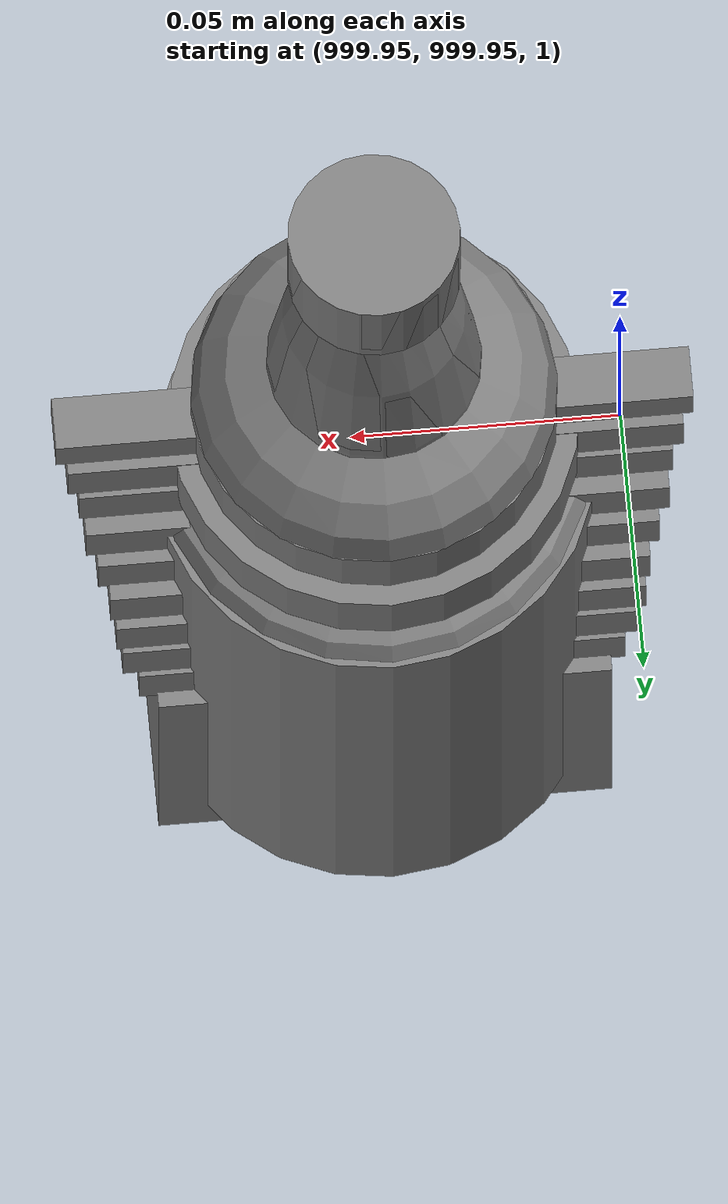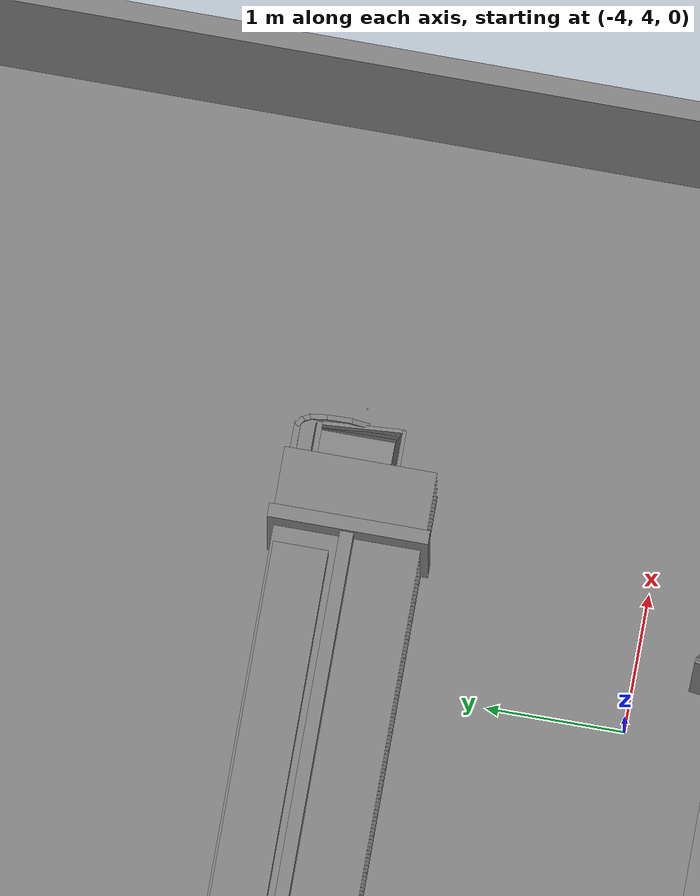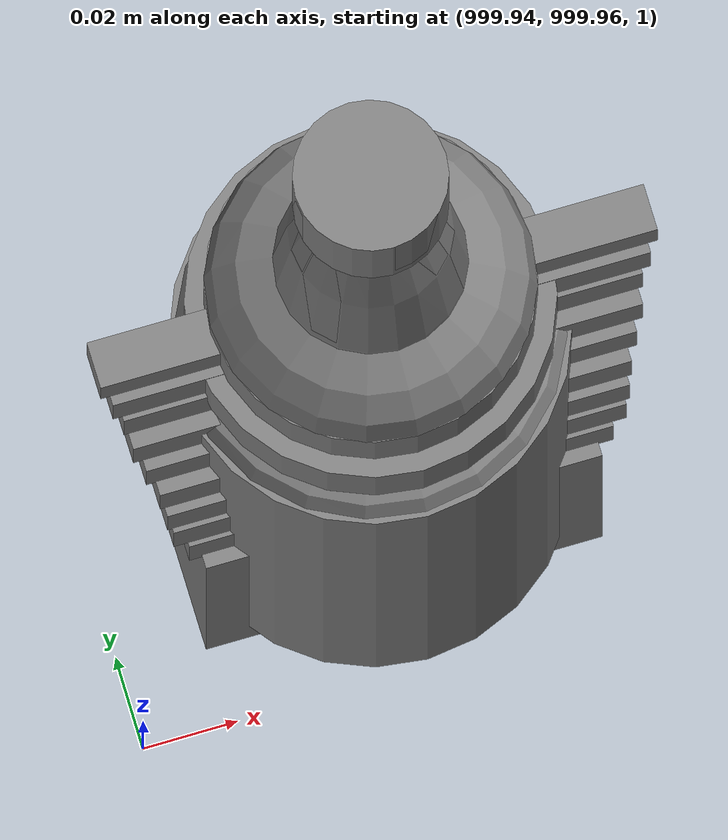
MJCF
<mujoco>
    <option gravity="0.000000000 0.000000000 -9.810000420" timestep="0.0166666" integrator="implicitfast" density="1.225" viscosity="1.8000001e-05" noslip_iterations="10" iterations="100" sdf_iterations="50">
        <flag multiccd="disable"/>
    </option>
    <size memory="1000M"/>
    <compiler coordinate="local"/>
    <worldbody>
        <light cutoff="30" pos="0 1 1" dir="0 -1 -2"/>
        <light cutoff="30" pos="0 -1 1" dir="0 1 -2"/>
        <body pos="-7.168000221 2.823999882 1.227496982" euler="-0.283413976 0.056829724 -0.133293271" name="openloong_gripper_2f85_fix_base_usda_Pos">
            <geom contype="1" conaffinity="1" density="1000" type="box" material="" rgba="0.500000000 0.500000000 0.500000000 1.000000000" solimp="0.899999976 0.949999988 0.001000000" friction="1.000000000 0.005000000 0.000100000" solref="0.020000000 1.000000000" margin="0" condim="3" group="0" pos="-0.002278805 0.074524641 -0.004134059" quat="0.315989345 0.948763072 -0.000000000 0.000000000" size="0.059999999 0.013000000 0.035000000" name="openloong_gripper_2f85_fix_base_usda_geom_9426F9E8_57FA_4C9F_AB5C_89FC90A5A827"/>
            <geom contype="1" conaffinity="1" density="1000" type="box" material="" rgba="0.500000000 0.500000000 0.500000000 1.000000000" solimp="0.899999976 0.949999988 0.001000000" friction="1.000000000 0.005000000 0.000100000" solref="0.020000000 1.000000000" margin="0" condim="3" group="0" pos="-0.002278805 0.078031301 0.008128285" quat="0.990447521 -0.137893379 -0.000000000 -0.000000000" size="0.059999999 0.010000000 0.035000000" name="openloong_gripper_2f85_fix_base_usda_geom_409B3DDF_94EA_4CEC_A3A3_0957E90BE993"/>
            <geom contype="1" conaffinity="1" density="1000" type="box" material="" rgba="0.500000000 0.500000000 0.500000000 1.000000000" solimp="0.899999976 0.949999988 0.001000000" friction="1.000000000 0.005000000 0.000100000" solref="0.020000000 1.000000000" margin="0" condim="3" group="0" pos="-0.002278805 0.080785275 -0.002596974" quat="0.287325472 -0.957833409 0.000000000 -0.000000000" size="0.059999999 0.013000000 0.035000000" name="openloong_gripper_2f85_fix_base_usda_geom_B54F2D28_874E_4593_BD64_41C7C6F3A222"/>
            <geom contype="1" conaffinity="1" density="1000" type="box" material="" rgba="0.500000000 0.500000000 0.500000000 1.000000000" solimp="0.899999976 0.949999988 0.001000000" friction="1.000000000 0.005000000 0.000100000" solref="0.020000000 1.000000000" margin="0" condim="3" group="0" pos="-0.002278805 -0.098804474 -0.020146966" quat="0.988851666 0.148906454 0.000000000 -0.000000000" size="0.059999999 0.022000000 0.020000000" name="openloong_gripper_2f85_fix_base_usda_geom_46D9730A_321F_43A7_94AB_484E043E559E"/>
            <geom contype="1" conaffinity="1" density="1000" type="box" material="" rgba="0.500000000 0.500000000 0.500000000 1.000000000" solimp="0.899999976 0.949999988 0.001000000" friction="1.000000000 0.005000000 0.000100000" solref="0.020000000 1.000000000" margin="0" condim="3" group="0" pos="-0.002279282 0.019920111 0.012102962" quat="0.995421767 0.095583342 -0.000000000 -0.000000000" size="0.059999999 0.025000000 0.026000001" name="openloong_gripper_2f85_fix_base_usda_geom_3CD0CFCB_2D11_4C8F_AD1B_FB82EF0F0DBA"/>
            <geom contype="1" conaffinity="1" density="1000" type="box" material="" rgba="0.500000000 0.500000000 0.500000000 1.000000000" solimp="0.899999976 0.949999988 0.001000000" friction="1.000000000 0.005000000 0.000100000" solref="0.020000000 1.000000000" margin="0" condim="3" group="0" pos="-0.002279282 0.005734444 -0.014276862" quat="0.999571741 -0.029275302 -0.000000000 -0.000000000" size="0.059999999 0.050000001 0.010000000" name="openloong_gripper_2f85_fix_base_usda_geom_F40A05C0_EBD8_4383_A0E3_C53D8A10FEB8"/>
            <geom contype="1" conaffinity="1" density="1000" type="box" material="" rgba="0.500000000 0.500000000 0.500000000 1.000000000" solimp="0.899999976 0.949999988 0.001000000" friction="1.000000000 0.005000000 0.000100000" solref="0.020000000 1.000000000" margin="0" condim="3" group="0" pos="-0.002278805 0.079460382 0.007771969" quat="0.922590554 -0.385781586 0.000000000 -0.000000000" size="0.059999999 0.010000000 0.035000000" name="openloong_gripper_2f85_fix_base_usda_geom_101397CE_C209_4583_B969_CE55AF6EFF44"/>
            <geom contype="1" conaffinity="1" density="1000" type="box" material="" rgba="0.500000000 0.500000000 0.500000000 1.000000000" solimp="0.899999976 0.949999988 0.001000000" friction="1.000000000 0.005000000 0.000100000" solref="0.020000000 1.000000000" margin="0" condim="3" group="0" pos="-0.002279282 0.081384182 -0.001320124" quat="0.590483785 -0.807049930 0.000000000 -0.000000000" size="0.059999999 0.013000000 0.035000000" name="openloong_gripper_2f85_fix_base_usda_geom_A8936970_A47F_43D8_A32C_F26B78286E71"/>
            <geom contype="1" conaffinity="1" density="1000" type="box" material="" rgba="0.500000000 0.500000000 0.500000000 1.000000000" solimp="0.899999976 0.949999988 0.001000000" friction="1.000000000 0.005000000 0.000100000" solref="0.020000000 1.000000000" margin="0" condim="3" group="0" pos="-0.002278805 -0.059297800 -0.007972836" quat="0.988851666 0.148906454 0.000000000 -0.000000000" size="0.059999999 0.020000000 0.022000000" name="openloong_gripper_2f85_fix_base_usda_geom_E2EA0624_2720_4C0A_A3F8_8E8A55E527EE"/>
            <geom contype="1" conaffinity="1" density="1000" type="box" material="" rgba="0.500000000 0.500000000 0.500000000 1.000000000" solimp="0.899999976 0.949999988 0.001000000" friction="1.000000000 0.005000000 0.000100000" solref="0.020000000 1.000000000" margin="0" condim="3" group="0" pos="-0.002278805 0.076618671 -0.004656792" quat="0.004634961 0.999989629 -0.000000000 0.000000000" size="0.059999999 0.013000000 0.035000000" name="openloong_gripper_2f85_fix_base_usda_geom_2DC8AAD7_D43A_450B_A3AE_4B36D543880F"/>
            <geom contype="1" conaffinity="1" density="1000" type="box" material="" rgba="0.500000000 0.500000000 0.500000000 1.000000000" solimp="0.899999976 0.949999988 0.001000000" friction="1.000000000 0.005000000 0.000100000" solref="0.020000000 1.000000000" margin="0" condim="3" group="0" pos="-0.002279282 -0.021952629 0.002960086" quat="0.991270423 0.131847665 -0.000000000 0.000000000" size="0.059999999 0.020000000 0.024000000" name="openloong_gripper_2f85_fix_base_usda_geom_FF534B8D_0E92_4AB7_85DD_BDAF51AFE292"/>
            <geom contype="1" conaffinity="1" density="1000" type="box" material="" rgba="0.500000000 0.500000000 0.500000000 1.000000000" solimp="0.899999976 0.949999988 0.001000000" friction="1.000000000 0.005000000 0.000100000" solref="0.020000000 1.000000000" margin="0" condim="3" group="0" pos="-0.002278805 0.081418991 0.002587914" quat="0.803492308 -0.595315695 0.000000000 -0.000000000" size="0.059999999 0.013000000 0.035000000" name="openloong_gripper_2f85_fix_base_usda_geom_C842A803_B365_44F4_A839_DCB90914C6AF"/>
            <geom contype="1" conaffinity="1" density="1000" type="box" material="" rgba="0.500000000 0.500000000 0.500000000 1.000000000" solimp="0.899999976 0.949999988 0.001000000" friction="1.000000000 0.005000000 0.000100000" solref="0.020000000 1.000000000" margin="0" condim="3" group="0" pos="-0.002278805 0.061115503 0.008545756" quat="0.999326169 0.036714450 0.000000000 -0.000000000" size="0.059999999 0.020000000 0.035000000" name="openloong_gripper_2f85_fix_base_usda_geom_205FD6CC_C970_4948_935A_22657FD14853"/>
            <freejoint name="openloong_gripper_2f85_fix_base_usda_pos_scan"/>
        </body>
        <body pos="-2.246559858 6.675261497 1.792272210" euler="-105.932334900 33.228805542 107.046958923" mocap="true" name="spotlight3_SpotLight"/>
        <body pos="1000.000000000 1000.000000000 1.000000000" euler="0.000000000 0.000000000 0.000000000" name="openloong_gripper_2f85_fix_base_usda_bottle_red">
            <geom contype="1" conaffinity="1" density="1000" type="ellipsoid" material="" rgba="0.500000000 0.500000000 0.500000000 1.000000000" solimp="0.899999976 0.949999988 0.001000000" friction="1.000000000 0.005000000 0.000100000" solref="0.020000000 1.000000000" margin="0" condim="3" group="0" pos="0.000000000 0.000000000 0.144284487" quat="1.000000000 0.000000000 0.000000000 0.000000000" size="0.021000000 0.021000000 0.079999998" name="openloong_gripper_2f85_fix_base_usda_geom_AF9099A8_7374_4B2D_92CD_01670E96DFC1"/>
            <geom contype="1" conaffinity="1" density="1000" type="cylinder" material="" rgba="0.500000000 0.500000000 0.500000000 1.000000000" solimp="0.899999976 0.949999988 0.001000000" friction="1.000000000 0.005000000 0.000100000" solref="0.020000000 1.000000000" margin="0" condim="3" group="0" pos="0.000000000 0.000000000 0.220618963" quat="1.000000000 0.000000000 0.000000000 0.000000000" size="0.016000001 0.010000000 1.000000000" name="openloong_gripper_2f85_fix_base_usda_geom_BDEF4AC1_BB9C_4C20_A241_0511915F23C4"/>
            <geom contype="1" conaffinity="1" density="1000" type="ellipsoid" material="" rgba="0.500000000 0.500000000 0.500000000 1.000000000" solimp="0.899999976 0.949999988 0.001000000" friction="1.000000000 0.005000000 0.000100000" solref="0.020000000 1.000000000" margin="0" condim="3" group="0" pos="0.000000000 0.000000000 0.118945479" quat="1.000000000 0.000000000 0.000000000 0.000000000" size="0.030999999 0.030999999 0.029999999" name="openloong_gripper_2f85_fix_base_usda_geom_A0D52A09_25F7_4157_BF2F_61164C98EDA0"/>
            <geom contype="1" conaffinity="1" density="1000" type="box" material="" rgba="0.500000000 0.500000000 0.500000000 1.000000000" solimp="0.899999976 0.949999988 0.001000000" friction="1.000000000 0.005000000 0.000100000" solref="0.020000000 1.000000000" margin="0" condim="3" group="0" pos="0.000000000 0.000000000 0.002189159" quat="1.000000000 0.000000000 0.000000000 0.000000000" size="0.020000000 0.020000000 0.003000000" name="openloong_gripper_2f85_fix_base_usda_geom_C1FE8315_B7B1_4910_AD33_5FBCF7C32B47"/>
            <geom contype="1" conaffinity="1" density="1000" type="cylinder" material="" rgba="0.500000000 0.500000000 0.500000000 1.000000000" solimp="0.899999976 0.949999988 0.001000000" friction="1.000000000 0.005000000 0.000100000" solref="0.020000000 1.000000000" margin="0" condim="3" group="0" pos="0.000000000 -0.000366211 0.060884237" quat="1.000000000 0.000000000 0.000000000 0.000000000" size="0.030999999 0.057999998 1.000000000" name="openloong_gripper_2f85_fix_base_usda_geom_895D1522_1BD1_43DB_868F_8E28DE9E74E6"/>
            <freejoint name="openloong_gripper_2f85_fix_base_usda_bottle_red_joint"/>
            <site size="0.005000000 0.005000000 0.005000000" rgba="0.500000000 0.500000000 0.500000000 1.000000000" pos="0.000000000 0.000000000 0.000000000" quat="0.999961913 0.008726535 0.000000000 0.000000000" group="0" type="sphere" name="openloong_gripper_2f85_fix_base_usda_bottle_redsite"/>
        </body>
        <body pos="1000.000000000 1000.000000000 1.000000000" euler="0.000000000 0.000000000 0.000000000" name="openloong_gripper_2f85_fix_base_usda_can">
            <geom contype="1" conaffinity="1" density="1000" type="cylinder" material="" rgba="0.500000000 0.500000000 0.500000000 1.000000000" solimp="0.899999976 0.949999988 0.001000000" friction="1.000000000 0.005000000 0.000100000" solref="0.020000000 1.000000000" margin="0" condim="3" group="0" pos="0.000000000 0.000000000 0.079676986" quat="1.000000000 0.000000000 0.000000000 0.000000000" size="0.034000002 0.071999997 1.000000000" name="openloong_gripper_2f85_fix_base_usda_geom_3A2D474E_7039_4AF9_8EC2_E91D0C3DB6F5"/>
            <geom contype="1" conaffinity="1" density="1000" type="ellipsoid" material="" rgba="0.500000000 0.500000000 0.500000000 1.000000000" solimp="0.899999976 0.949999988 0.001000000" friction="1.000000000 0.005000000 0.000100000" solref="0.020000000 1.000000000" margin="0" condim="3" group="0" pos="0.000000000 0.000000000 0.151854277" quat="1.000000000 0.000000000 0.000000000 0.000000000" size="0.034000002 0.034000002 0.020000000" name="openloong_gripper_2f85_fix_base_usda_geom_1136A8A6_28A5_4C85_ACC1_91CA3A183057"/>
            <geom contype="1" conaffinity="1" density="1000" type="box" material="" rgba="0.500000000 0.500000000 0.500000000 1.000000000" solimp="0.899999976 0.949999988 0.001000000" friction="1.000000000 0.005000000 0.000100000" solref="0.020000000 1.000000000" margin="0" condim="3" group="0" pos="0.000000000 0.000000000 0.004777670" quat="1.000000000 0.000000000 0.000000000 0.000000000" size="0.020000000 0.020000000 0.005000000" name="openloong_gripper_2f85_fix_base_usda_geom_5C127296_A64E_4A20_9E2D_7883D0F58F88"/>
            <freejoint name="openloong_gripper_2f85_fix_base_usda_can_joint"/>
            <site size="0.005000000 0.005000000 0.005000000" rgba="0.500000000 0.500000000 0.500000000 1.000000000" pos="0.000000000 0.000000000 0.000000000" quat="1.000000000 0.000000000 0.000000000 0.000000000" group="0" type="sphere" name="openloong_gripper_2f85_fix_base_usda_cansite"/>
        </body>
        <body pos="1000.000000000 1000.000000000 1.000000000" euler="0.000000000 0.000000000 0.000000000" name="openloong_gripper_2f85_fix_base_usda_jar_01">
            <geom contype="1" conaffinity="1" density="1000" type="box" material="" rgba="0.500000000 0.500000000 0.500000000 1.000000000" solimp="0.899999976 0.949999988 0.001000000" friction="1.000000000 0.005000000 0.000100000" solref="0.020000000 1.000000000" margin="0" condim="3" group="0" pos="0.000000000 0.000000000 0.006158113" quat="1.000000000 0.000000000 0.000000000 0.000000000" size="0.020000000 0.020000000 0.005000000" name="openloong_gripper_2f85_fix_base_usda_geom_69DB82A1_EF3C_40D2_ACC1_359A04AEFE8E"/>
            <geom contype="1" conaffinity="1" density="1000" type="cylinder" material="" rgba="0.500000000 0.500000000 0.500000000 1.000000000" solimp="0.899999976 0.949999988 0.001000000" friction="1.000000000 0.005000000 0.000100000" solref="0.020000000 1.000000000" margin="0" condim="3" group="0" pos="0.000000000 0.000000000 0.062744498" quat="1.000000000 0.000000000 0.000000000 0.000000000" size="0.041000001 0.052999999 1.000000000" name="openloong_gripper_2f85_fix_base_usda_geom_AD0B5005_AB15_4DE5_95C7_3443DD1FEA88"/>
            <geom contype="1" conaffinity="1" density="1000" type="ellipsoid" material="" rgba="0.500000000 0.500000000 0.500000000 1.000000000" solimp="0.899999976 0.949999988 0.001000000" friction="1.000000000 0.005000000 0.000100000" solref="0.020000000 1.000000000" margin="0" condim="3" group="0" pos="0.000000000 0.000000000 0.122252703" quat="1.000000000 0.000000000 0.000000000 0.000000000" size="0.035999998 0.035999998 0.010000000" name="openloong_gripper_2f85_fix_base_usda_geom_5F9DE80A_2832_4265_B2F1_EDE77F602EDB"/>
            <geom contype="1" conaffinity="1" density="1000" type="cylinder" material="" rgba="0.500000000 0.500000000 0.500000000 1.000000000" solimp="0.899999976 0.949999988 0.001000000" friction="1.000000000 0.005000000 0.000100000" solref="0.020000000 1.000000000" margin="0" condim="3" group="0" pos="0.000000000 0.000000000 0.015747190" quat="1.000000000 0.000000000 0.000000000 0.000000000" size="0.035000000 0.010000000 1.000000000" name="openloong_gripper_2f85_fix_base_usda_geom_978F99F9_288B_4C80_9A79_523A82EAF9C7"/>
            <geom contype="1" conaffinity="1" density="1000" type="ellipsoid" material="" rgba="0.500000000 0.500000000 0.500000000 1.000000000" solimp="0.899999976 0.949999988 0.001000000" friction="1.000000000 0.005000000 0.000100000" solref="0.020000000 1.000000000" margin="0" condim="3" group="0" pos="0.000000000 0.000000000 0.115815401" quat="1.000000000 0.000000000 0.000000000 0.000000000" size="0.039999999 0.039999999 0.010000000" name="openloong_gripper_2f85_fix_base_usda_geom_BB568812_4778_4BDF_ADD6_488FA906B303"/>
            <geom contype="1" conaffinity="1" density="1000" type="cylinder" material="" rgba="0.500000000 0.500000000 0.500000000 1.000000000" solimp="0.899999976 0.949999988 0.001000000" friction="1.000000000 0.005000000 0.000100000" solref="0.020000000 1.000000000" margin="0" condim="3" group="0" pos="0.000000000 0.000000000 0.133183479" quat="1.000000000 0.000000000 0.000000000 0.000000000" size="0.037999999 0.006500000 1.000000000" name="openloong_gripper_2f85_fix_base_usda_geom_19998D98_1942_455F_8B92_47D4F64C6804"/>
            <freejoint name="openloong_gripper_2f85_fix_base_usda_jar_01_joint"/>
            <site size="0.005000000 0.005000000 0.005000000" rgba="0.500000000 0.500000000 0.500000000 1.000000000" pos="0.000000000 0.000000000 0.000000000" quat="1.000000000 0.000000000 0.000000000 0.000000000" group="0" type="sphere" name="openloong_gripper_2f85_fix_base_usda_jar_01site"/>
        </body>
        <body pos="1000.000000000 1000.000000000 1.000000000" euler="0.000000000 0.000000000 0.000000000" name="openloong_gripper_2f85_fix_base_usda_bottle_blue">
            <geom contype="1" conaffinity="1" density="1000" type="ellipsoid" material="" rgba="0.500000000 0.500000000 0.500000000 1.000000000" solimp="0.899999976 0.949999988 0.001000000" friction="1.000000000 0.005000000 0.000100000" solref="0.020000000 1.000000000" margin="0" condim="3" group="0" pos="0.000000000 0.000000000 0.118920922" quat="1.000000000 0.000000000 0.000000000 0.000000000" size="0.030999999 0.030999999 0.029999999" name="openloong_gripper_2f85_fix_base_usda_geom_31BDACD3_004A_429E_913D_67B20293395C"/>
            <geom contype="1" conaffinity="1" density="1000" type="box" material="" rgba="0.500000000 0.500000000 0.500000000 1.000000000" solimp="0.899999976 0.949999988 0.001000000" friction="1.000000000 0.005000000 0.000100000" solref="0.020000000 1.000000000" margin="0" condim="3" group="0" pos="0.000000000 0.000000000 0.002164602" quat="1.000000000 0.000000000 0.000000000 0.000000000" size="0.020000000 0.020000000 0.003000000" name="openloong_gripper_2f85_fix_base_usda_geom_B128FB86_C816_4BD7_B7EB_BD9C2380F42B"/>
            <geom contype="1" conaffinity="1" density="1000" type="cylinder" material="" rgba="0.500000000 0.500000000 0.500000000 1.000000000" solimp="0.899999976 0.949999988 0.001000000" friction="1.000000000 0.005000000 0.000100000" solref="0.020000000 1.000000000" margin="0" condim="3" group="0" pos="0.000000000 -0.000366211 0.060859680" quat="1.000000000 0.000000000 0.000000000 0.000000000" size="0.030999999 0.057999998 1.000000000" name="openloong_gripper_2f85_fix_base_usda_geom_ACDCBFC5_BB39_4A3A_A0CD_AA79EF140602"/>
            <geom contype="1" conaffinity="1" density="1000" type="cylinder" material="" rgba="0.500000000 0.500000000 0.500000000 1.000000000" solimp="0.899999976 0.949999988 0.001000000" friction="1.000000000 0.005000000 0.000100000" solref="0.020000000 1.000000000" margin="0" condim="3" group="0" pos="0.000000000 0.000000000 0.220594406" quat="1.000000000 0.000000000 0.000000000 0.000000000" size="0.016000001 0.010000000 1.000000000" name="openloong_gripper_2f85_fix_base_usda_geom_BD47D491_3083_4541_BE12_4D36208CE941"/>
            <geom contype="1" conaffinity="1" density="1000" type="ellipsoid" material="" rgba="0.500000000 0.500000000 0.500000000 1.000000000" solimp="0.899999976 0.949999988 0.001000000" friction="1.000000000 0.005000000 0.000100000" solref="0.020000000 1.000000000" margin="0" condim="3" group="0" pos="0.000000000 0.000000000 0.144259930" quat="1.000000000 0.000000000 0.000000000 0.000000000" size="0.021000000 0.021000000 0.079999998" name="openloong_gripper_2f85_fix_base_usda_geom_3FF3663A_55F0_461B_B31D_6EB49BAB3268"/>
            <freejoint name="openloong_gripper_2f85_fix_base_usda_bottle_blue_joint"/>
            <site size="0.005000000 0.005000000 0.005000000" rgba="0.500000000 0.500000000 0.500000000 1.000000000" pos="0.000000000 0.000000000 0.000000000" quat="0.999961913 0.008726535 0.000000000 0.000000000" group="0" type="sphere" name="openloong_gripper_2f85_fix_base_usda_bottle_bluesite"/>
        </body>
        <body pos="-2.339632034 6.361300945 1.756921053" euler="-100.634292603 42.970691681 92.711914062" mocap="true" name="spotlight2_SpotLight"/>
        <body pos="-2.266637802 6.274727821 1.757892370" euler="-116.297416687 27.568832397 -43.075794220" mocap="true" name="spotlight1_SpotLight"/>
        <body pos="1000.000000000 1000.000000000 1.000000000" euler="0.000000000 0.000000000 0.000000000" name="openloong_gripper_2f85_fix_base_usda_salt">
            <geom contype="1" conaffinity="1" density="1000" type="box" material="" rgba="0.500000000 0.500000000 0.500000000 1.000000000" solimp="0.899999976 0.949999988 0.001000000" friction="1.000000000 0.005000000 0.000100000" solref="0.020000000 1.000000000" margin="0" condim="3" group="0" pos="0.000305176 0.000000000 0.084862232" quat="1.000000000 0.000000000 0.000000000 0.000000000" size="0.048999999 0.018999999 0.005000000" name="openloong_gripper_2f85_fix_base_usda_geom_CC4787B1_6E48_4FC3_8860_A627A59DCD3F"/>
            <geom contype="1" conaffinity="1" density="1000" type="box" material="" rgba="0.500000000 0.500000000 0.500000000 1.000000000" solimp="0.899999976 0.949999988 0.001000000" friction="1.000000000 0.005000000 0.000100000" solref="0.020000000 1.000000000" margin="0" condim="3" group="0" pos="0.000305176 0.000000000 0.104564309" quat="1.000000000 0.000000000 0.000000000 0.000000000" size="0.052000001 0.014000000 0.005000000" name="openloong_gripper_2f85_fix_base_usda_geom_17A159E3_7430_4FCE_9373_ACE6FCDF6F0E"/>
            <geom contype="1" conaffinity="1" density="1000" type="box" material="" rgba="0.500000000 0.500000000 0.500000000 1.000000000" solimp="0.899999976 0.949999988 0.001000000" friction="1.000000000 0.005000000 0.000100000" solref="0.020000000 1.000000000" margin="0" condim="3" group="0" pos="0.000305176 0.000000000 0.114487171" quat="1.000000000 0.000000000 0.000000000 0.000000000" size="0.054000001 0.011500000 0.005000000" name="openloong_gripper_2f85_fix_base_usda_geom_6BF0EDE8_4EF3_4A91_B42E_67FABCDBFC98"/>
            <geom contype="1" conaffinity="1" density="1000" type="box" material="" rgba="0.500000000 0.500000000 0.500000000 1.000000000" solimp="0.899999976 0.949999988 0.001000000" friction="1.000000000 0.005000000 0.000100000" solref="0.020000000 1.000000000" margin="0" condim="3" group="0" pos="0.000305176 0.000000000 0.075103164" quat="1.000000000 0.000000000 0.000000000 0.000000000" size="0.048000000 0.020000000 0.005000000" name="openloong_gripper_2f85_fix_base_usda_geom_92EBD0F2_ADBB_4C52_9A40_2D6247C50D24"/>
            <geom contype="1" conaffinity="1" density="1000" type="box" material="" rgba="0.500000000 0.500000000 0.500000000 1.000000000" solimp="0.899999976 0.949999988 0.001000000" friction="1.000000000 0.005000000 0.000100000" solref="0.020000000 1.000000000" margin="0" condim="3" group="0" pos="0.000305176 0.000000000 0.134892464" quat="1.000000000 0.000000000 0.000000000 0.000000000" size="0.057000000 0.007000000 0.005000000" name="openloong_gripper_2f85_fix_base_usda_geom_3D55FBD5_D976_4BA4_B4F5_610FCB61A034"/>
            <geom contype="1" conaffinity="1" density="1000" type="box" material="" rgba="0.500000000 0.500000000 0.500000000 1.000000000" solimp="0.899999976 0.949999988 0.001000000" friction="1.000000000 0.005000000 0.000100000" solref="0.020000000 1.000000000" margin="0" condim="3" group="0" pos="0.000305176 0.000000000 0.094920278" quat="1.000000000 0.000000000 0.000000000 0.000000000" size="0.050000001 0.017000001 0.005000000" name="openloong_gripper_2f85_fix_base_usda_geom_B6A90764_9A1E_4EFF_86ED_FA5ECFA7384F"/>
            <geom contype="1" conaffinity="1" density="1000" type="box" material="" rgba="0.500000000 0.500000000 0.500000000 1.000000000" solimp="0.899999976 0.949999988 0.001000000" friction="1.000000000 0.005000000 0.000100000" solref="0.020000000 1.000000000" margin="0" condim="3" group="0" pos="0.000305176 0.000000000 0.065204859" quat="1.000000000 0.000000000 0.000000000 0.000000000" size="0.045000002 0.021000000 0.005000000" name="openloong_gripper_2f85_fix_base_usda_geom_7CDB5E99_FFB2_40E3_9188_18EE5D33286E"/>
            <geom contype="1" conaffinity="1" density="1000" type="box" material="" rgba="0.500000000 0.500000000 0.500000000 1.000000000" solimp="0.899999976 0.949999988 0.001000000" friction="1.000000000 0.005000000 0.000100000" solref="0.020000000 1.000000000" margin="0" condim="3" group="0" pos="0.000305176 0.000000000 0.144135714" quat="1.000000000 0.000000000 0.000000000 0.000000000" size="0.059000000 0.005000000 0.004000000" name="openloong_gripper_2f85_fix_base_usda_geom_B3847647_12C6_40AB_B0BF_CC650BCAB0A5"/>
            <geom contype="1" conaffinity="1" density="1000" type="box" material="" rgba="0.500000000 0.500000000 0.500000000 1.000000000" solimp="0.899999976 0.949999988 0.001000000" friction="1.000000000 0.005000000 0.000100000" solref="0.020000000 1.000000000" margin="0" condim="3" group="0" pos="0.000000000 0.000000000 0.031593561" quat="1.000000000 0.000000000 0.000000000 0.000000000" size="0.041999999 0.024000000 0.029999999" name="openloong_gripper_2f85_fix_base_usda_geom_57D79A95_D739_4AD4_868D_718B6F2C90B7"/>
            <geom contype="1" conaffinity="1" density="1000" type="box" material="" rgba="0.500000000 0.500000000 0.500000000 1.000000000" solimp="0.899999976 0.949999988 0.001000000" friction="1.000000000 0.005000000 0.000100000" solref="0.020000000 1.000000000" margin="0" condim="3" group="0" pos="0.000305176 0.000000000 0.124608755" quat="1.000000000 0.000000000 0.000000000 0.000000000" size="0.055000000 0.008000000 0.005000000" name="openloong_gripper_2f85_fix_base_usda_geom_79F77D5B_D6F9_4C98_B296_F099408805C0"/>
            <freejoint name="openloong_gripper_2f85_fix_base_usda_salt_joint"/>
            <site size="0.005000000 0.005000000 0.005000000" rgba="0.500000000 0.500000000 0.500000000 1.000000000" pos="0.000000000 0.000000000 0.000000000" quat="1.000000000 0.000000000 0.000000000 0.000000000" group="0" type="sphere" name="openloong_gripper_2f85_fix_base_usda_saltsite"/>
        </body>
        <body pos="0.000000000 0.000000000 0.000000000" euler="0.000000000 0.000000000 0.000000000" name=" Static Objects_ Static Objects">
            <geom contype="1" conaffinity="1" density="1000" type="box" material="" rgba="0.500000000 0.500000000 0.500000000 1.000000000" solimp="0.899999976 0.949999988 0.001000000" friction="1.000000000 0.005000000 0.000100000" solref="0.020000000 1.000000000" margin="0" condim="3" group="0" pos="-3.101639986 6.150595188 1.018643856" quat="1.000000000 0.000000000 0.000000000 0.000000000" size="0.050000001 0.579999983 1.019999981" name=" Static Objects_geom_42818DD6_0E1B_4D43_B855_2C2C87F1D85F"/>
            <geom contype="1" conaffinity="1" density="1000" type="box" material="" rgba="0.500000000 0.500000000 0.500000000 1.000000000" solimp="0.899999976 0.949999988 0.001000000" friction="1.000000000 0.005000000 0.000100000" solref="0.020000000 1.000000000" margin="0" condim="3" group="0" pos="-2.825197220 6.153595448 1.115278244" quat="0.707107067 0.000000000 0.000000000 0.707106471" size="0.550000012 0.239999995 0.025000000" name=" Static Objects_geom_D878F26A_6331_4D95_8AC1_E4D8C8DBF13E"/>
            <geom contype="1" conaffinity="1" density="1000" type="box" material="" rgba="0.500000000 0.500000000 0.500000000 1.000000000" solimp="0.899999976 0.949999988 0.001000000" friction="1.000000000 0.005000000 0.000100000" solref="0.020000000 1.000000000" margin="0" condim="3" group="0" pos="-2.825197220 6.153595448 0.097434282" quat="0.707107067 0.000000000 0.000000000 0.707106471" size="0.550000012 0.239999995 0.098999999" name=" Static Objects_geom_73FCA96E_0882_46F4_B661_80625AB7F8E2"/>
            <geom contype="1" conaffinity="1" density="1000" type="box" material="" rgba="0.500000000 0.500000000 0.500000000 1.000000000" solimp="0.899999976 0.949999988 0.001000000" friction="1.000000000 0.005000000 0.000100000" solref="0.020000000 1.000000000" margin="0" condim="3" group="0" pos="-6.293097973 6.153595448 1.114443064" quat="0.707107067 0.000000000 0.000000000 0.707106471" size="0.529999971 3.134999990 0.025000000" name=" Static Objects_geom_23F10DB2_1B45_4EE7_82ED_A19906EB77B6"/>
            <geom contype="1" conaffinity="1" density="1000" type="box" material="" rgba="0.500000000 0.500000000 0.500000000 1.000000000" solimp="0.899999976 0.949999988 0.001000000" friction="1.000000000 0.005000000 0.000100000" solref="0.020000000 1.000000000" margin="0" condim="3" group="0" pos="-2.825197220 6.153595448 1.563861728" quat="0.707107067 0.000000000 0.000000000 0.707106471" size="0.550000012 0.239999995 0.025000000" name=" Static Objects_geom_7A7C4B65_A2BB_4BE1_90DD_69622ED0B210"/>
            <geom contype="1" conaffinity="1" density="1000" type="box" material="" rgba="0.500000000 0.500000000 0.500000000 1.000000000" solimp="0.899999976 0.949999988 0.001000000" friction="1.000000000 0.005000000 0.000100000" solref="0.020000000 1.000000000" margin="0" condim="3" group="0" pos="-6.311686516 6.153595448 1.018643856" quat="0.707107067 0.000000000 0.000000000 0.707106471" size="0.050000001 3.150000095 1.019999981" name=" Static Objects_geom_624247F1_7399_4BD1_BE0E_51E7506CF09F"/>
            <geom contype="1" conaffinity="1" density="1000" type="box" material="" rgba="0.500000000 0.500000000 0.500000000 1.000000000" solimp="0.899999976 0.949999988 0.001000000" friction="1.000000000 0.005000000 0.000100000" solref="0.020000000 1.000000000" margin="0" condim="3" group="0" pos="-6.286010742 6.153595448 0.096129179" quat="0.707107067 0.000000000 0.000000000 0.707106471" size="0.529999971 3.134999990 0.098999999" name=" Static Objects_geom_887AEDB4_97CF_4E10_8E5F_D99AB10CA5F5"/>
            <geom contype="1" conaffinity="1" density="1000" type="box" material="" rgba="0.500000000 0.500000000 0.500000000 1.000000000" solimp="0.899999976 0.949999988 0.001000000" friction="1.000000000 0.005000000 0.000100000" solref="0.020000000 1.000000000" margin="0" condim="3" group="0" pos="-2.825197220 6.153595448 0.629031777" quat="0.707107067 0.000000000 0.000000000 0.707106471" size="0.550000012 0.239999995 0.025000000" name=" Static Objects_geom_340EA47E_DB60_4235_BECB_939D1E69B190"/>
            <geom contype="1" conaffinity="1" density="1000" type="box" material="" rgba="0.500000000 0.500000000 0.500000000 1.000000000" solimp="0.899999976 0.949999988 0.001000000" friction="1.000000000 0.005000000 0.000100000" solref="0.020000000 1.000000000" margin="0" condim="3" group="0" pos="-6.286010742 6.153595448 1.563861728" quat="0.707107067 0.000000000 0.000000000 0.707106471" size="0.529999971 3.134999990 0.025000000" name=" Static Objects_geom_23C723D1_E445_4289_A066_3581EB3965F3"/>
            <geom contype="1" conaffinity="1" density="1000" type="box" material="" rgba="0.500000000 0.500000000 0.500000000 1.000000000" solimp="0.899999976 0.949999988 0.001000000" friction="1.000000000 0.005000000 0.000100000" solref="0.020000000 1.000000000" margin="0" condim="3" group="0" pos="-6.286010742 6.153595448 0.629031777" quat="0.707107067 0.000000000 0.000000000 0.707106471" size="0.529999971 3.134999990 0.025000000" name=" Static Objects_geom_611F9252_4F26_42AE_B6DD_5700447FF99F"/>
            <geom contype="1" conaffinity="1" density="1000" type="box" material="" rgba="0.500000000 0.500000000 0.500000000 1.000000000" solimp="0.899999976 0.949999988 0.001000000" friction="1.000000000 0.005000000 0.000100000" solref="0.020000000 1.000000000" margin="0" condim="3" group="0" pos="-7.719123363 2.867671013 1.173410416" quat="1.000000000 0.000000000 0.000000000 0.000000000" size="0.250000000 0.250000000 0.079999998" name=" Static Objects_geom_DB7BC579_E0DF_46F0_B6E8_B48359AEA722"/>
            <geom contype="1" conaffinity="1" density="1000" type="box" material="" rgba="0.500000000 0.500000000 0.500000000 1.000000000" solimp="0.899999976 0.949999988 0.001000000" friction="1.000000000 0.005000000 0.000100000" solref="0.020000000 1.000000000" margin="0" condim="3" group="0" pos="-7.408766270 3.088089943 1.776644945" quat="0.928051054 0.000000000 0.000000000 0.372453064" size="0.050000001 0.100000001 0.050000001" name=" Static Objects_geom_71936B3E_5871_4672_923A_4C70FBDC22C4"/>
            <geom contype="1" conaffinity="1" density="1000" type="box" material="" rgba="0.500000000 0.500000000 0.500000000 1.000000000" solimp="0.899999976 0.949999988 0.001000000" friction="1.000000000 0.005000000 0.000100000" solref="0.020000000 1.000000000" margin="0" condim="3" group="0" pos="-7.719123363 2.958004713 1.530241251" quat="1.000000000 0.000000000 0.000000000 0.000000000" size="0.250000000 0.159999996 0.280000001" name=" Static Objects_geom_CAEAA639_391A_4FD4_9335_B8952AF567F0"/>
            <geom contype="1" conaffinity="1" density="1000" type="cylinder" material="" rgba="0.500000000 0.500000000 0.500000000 1.000000000" solimp="0.899999976 0.949999988 0.001000000" friction="1.000000000 0.005000000 0.000100000" solref="0.020000000 1.000000000" margin="0" condim="3" group="0" pos="-7.427312374 3.069516420 1.502544641" quat="0.928051054 0.000000000 0.000000000 0.372453064" size="0.015000000 0.230000004 0.100000001" name=" Static Objects_geom_B2F13E26_3574_44AE_86BE_1F7B33067DF7"/>
            <geom contype="1" conaffinity="1" density="1000" type="box" material="" rgba="0.500000000 0.500000000 0.500000000 1.000000000" solimp="0.899999976 0.949999988 0.001000000" friction="1.000000000 0.005000000 0.000100000" solref="0.020000000 1.000000000" margin="0" condim="3" group="0" pos="-7.437745571 3.067511320 1.289965630" quat="1.000000000 0.000000000 0.000000000 0.000000000" size="0.029999999 0.020000000 0.020000000" name=" Static Objects_geom_93E1043C_7F52_48CB_99F6_4F815488A9B4"/>
            <geom contype="1" conaffinity="1" density="1000" type="box" material="" rgba="0.500000000 0.500000000 0.500000000 1.000000000" solimp="0.899999976 0.949999988 0.001000000" friction="1.000000000 0.005000000 0.000100000" solref="0.020000000 1.000000000" margin="0" condim="3" group="0" pos="-9.058088303 6.434794426 1.209077358" quat="1.000000000 0.000000000 0.000000000 0.000000000" size="0.250000000 0.100000001 0.070000000" name=" Static Objects_geom_9CDEE143_A110_4CEA_9DAA_573D872548B1"/>
            <geom contype="1" conaffinity="1" density="1000" type="box" material="" rgba="0.500000000 0.500000000 0.500000000 1.000000000" solimp="0.899999976 0.949999988 0.001000000" friction="1.000000000 0.005000000 0.000100000" solref="0.020000000 1.000000000" margin="0" condim="3" group="0" pos="-7.886891365 6.459744930 0.352518857" quat="1.000000000 0.000000000 0.000000000 0.000000000" size="1.500000000 0.200000003 0.150000006" name=" Static Objects_geom_9ABF9047_062F_4D7D_8F93_D539F6B7557A"/>
            <geom contype="1" conaffinity="1" density="1000" type="box" material="" rgba="0.500000000 0.500000000 0.500000000 1.000000000" solimp="0.899999976 0.949999988 0.001000000" friction="1.000000000 0.005000000 0.000100000" solref="0.020000000 1.000000000" margin="0" condim="3" group="0" pos="-9.237723351 6.464855671 1.209077358" quat="1.000000000 0.000000000 0.000000000 0.000000000" size="0.100000001 0.100000001 0.070000000" name=" Static Objects_geom_8EFBD506_BD2A_4980_A955_8037852F756A"/>
            <geom contype="1" conaffinity="1" density="1000" type="box" material="" rgba="0.500000000 0.500000000 0.500000000 1.000000000" solimp="0.899999976 0.949999988 0.001000000" friction="1.000000000 0.005000000 0.000100000" solref="0.020000000 1.000000000" margin="0" condim="3" group="0" pos="-6.924745083 6.362090111 1.214329123" quat="1.000000000 0.000000000 0.000000000 0.000000000" size="0.200000003 0.100000001 0.075000003" name=" Static Objects_geom_13510DFF_CFB4_4448_B725_6925000B739A"/>
            <geom contype="1" conaffinity="1" density="1000" type="box" material="" rgba="0.500000000 0.500000000 0.500000000 1.000000000" solimp="0.899999976 0.949999988 0.001000000" friction="1.000000000 0.005000000 0.000100000" solref="0.020000000 1.000000000" margin="0" condim="3" group="0" pos="-4.407354832 6.459744930 1.292199373" quat="1.000000000 0.000000000 0.000000000 0.000000000" size="1.240000010 0.200000003 0.150000006" name=" Static Objects_geom_42A3C409_5229_449B_B0BB_DB01B668B27C"/>
            <geom contype="1" conaffinity="1" density="1000" type="box" material="" rgba="0.500000000 0.500000000 0.500000000 1.000000000" solimp="0.899999976 0.949999988 0.001000000" friction="1.000000000 0.005000000 0.000100000" solref="0.020000000 1.000000000" margin="0" condim="3" group="0" pos="-5.611940861 6.318420410 0.350975692" quat="1.000000000 0.000000000 0.000000000 0.000000000" size="0.699999988 0.100000001 0.150000006" name=" Static Objects_geom_57023A68_FA23_45A0_97CF_921814D156FC"/>
            <geom contype="1" conaffinity="1" density="1000" type="box" material="" rgba="0.500000000 0.500000000 0.500000000 1.000000000" solimp="0.899999976 0.949999988 0.001000000" friction="1.000000000 0.005000000 0.000100000" solref="0.020000000 1.000000000" margin="0" condim="3" group="0" pos="-6.300771236 6.459744930 1.744376063" quat="1.000000000 0.000000000 0.000000000 0.000000000" size="3.000000000 0.200000003 0.150000006" name=" Static Objects_geom_7B8257B9_767D_465D_9314_726B004EA6CE"/>
            <geom contype="1" conaffinity="1" density="1000" type="box" material="" rgba="0.500000000 0.500000000 0.500000000 1.000000000" solimp="0.899999976 0.949999988 0.001000000" friction="1.000000000 0.005000000 0.000100000" solref="0.020000000 1.000000000" margin="0" condim="3" group="0" pos="-8.844120979 6.464855671 1.209077358" quat="1.000000000 0.000000000 0.000000000 0.000000000" size="0.100000001 0.100000001 0.070000000" name=" Static Objects_geom_BDFF71DE_2C9C_4B04_91B1_A0C2BB1A3713"/>
            <geom contype="1" conaffinity="1" density="1000" type="box" material="" rgba="0.500000000 0.500000000 0.500000000 1.000000000" solimp="0.899999976 0.949999988 0.001000000" friction="1.000000000 0.005000000 0.000100000" solref="0.020000000 1.000000000" margin="0" condim="3" group="0" pos="-6.824534416 6.447464466 1.212718010" quat="1.000000000 0.000000000 0.000000000 0.000000000" size="0.100000001 0.100000001 0.075000003" name=" Static Objects_geom_B5E0DBD2_00F5_4022_9386_0B3EC2CC97AE"/>
            <geom contype="1" conaffinity="1" density="1000" type="box" material="" rgba="0.500000000 0.500000000 0.500000000 1.000000000" solimp="0.899999976 0.949999988 0.001000000" friction="1.000000000 0.005000000 0.000100000" solref="0.020000000 1.000000000" margin="0" condim="3" group="0" pos="-6.751636982 6.459744930 0.800981164" quat="1.000000000 0.000000000 0.000000000 0.000000000" size="2.200000048 0.200000003 0.150000006" name=" Static Objects_geom_23DA60F4_9616_4B04_BC06_CE45141DDED6"/>
            <geom contype="1" conaffinity="1" density="1000" type="box" material="" rgba="0.500000000 0.500000000 0.500000000 1.000000000" solimp="0.899999976 0.949999988 0.001000000" friction="1.000000000 0.005000000 0.000100000" solref="0.020000000 1.000000000" margin="0" condim="3" group="0" pos="-6.098561764 6.327973843 1.292199373" quat="1.000000000 0.000000000 0.000000000 0.000000000" size="0.500000000 0.100000001 0.150000006" name=" Static Objects_geom_AF693DD5_876C_4420_B53F_25A37933A9AB"/>
            <geom contype="1" conaffinity="1" density="1000" type="box" material="" rgba="0.500000000 0.500000000 0.500000000 1.000000000" solimp="0.899999976 0.949999988 0.001000000" friction="1.000000000 0.005000000 0.000100000" solref="0.020000000 1.000000000" margin="0" condim="3" group="0" pos="-3.907610416 6.318625927 0.800981164" quat="1.000000000 0.000000000 0.000000000 0.000000000" size="0.500000000 0.100000001 0.150000006" name=" Static Objects_geom_A784FBD7_CA3E_408D_B35A_A8E9464FA3B6"/>
            <geom contype="1" conaffinity="1" density="1000" type="box" material="" rgba="0.500000000 0.500000000 0.500000000 1.000000000" solimp="0.899999976 0.949999988 0.001000000" friction="1.000000000 0.005000000 0.000100000" solref="0.020000000 1.000000000" margin="0" condim="3" group="0" pos="-7.373087406 6.458900928 1.214329123" quat="1.000000000 0.000000000 0.000000000 0.000000000" size="0.250000000 0.200000003 0.075000003" name=" Static Objects_geom_00997FDB_51DD_4299_B633_C330FDD39E6E"/>
            <geom contype="1" conaffinity="1" density="1000" type="box" material="" rgba="0.500000000 0.500000000 0.500000000 1.000000000" solimp="0.899999976 0.949999988 0.001000000" friction="1.000000000 0.005000000 0.000100000" solref="0.020000000 1.000000000" margin="0" condim="3" group="0" pos="-4.035642624 6.459744930 0.352518857" quat="1.000000000 0.000000000 0.000000000 0.000000000" size="0.800000012 0.200000003 0.150000006" name=" Static Objects_geom_1C279964_C75F_4867_88C5_72632C97FC53"/>
            <geom contype="1" conaffinity="1" density="1000" type="box" material="" rgba="0.500000000 0.500000000 0.500000000 1.000000000" solimp="0.899999976 0.949999988 0.001000000" friction="1.000000000 0.005000000 0.000100000" solref="0.020000000 1.000000000" margin="0" condim="3" group="0" pos="-6.460197449 2.937205315 0.548931718" quat="1.000000000 0.000000000 0.000000000 0.000000000" size="2.650000095 0.430000007 0.550000012" name=" Static Objects_geom_E9ACC624_9FA7_4FC0_9BC8_C92E9D39529B"/>
            <geom contype="1" conaffinity="1" density="1000" type="box" material="" rgba="0.500000000 0.500000000 0.500000000 1.000000000" solimp="0.899999976 0.949999988 0.001000000" friction="1.000000000 0.005000000 0.000100000" solref="0.020000000 1.000000000" margin="0" condim="3" group="0" pos="-4.240264893 1.327049494 0.549888909" quat="1.000000000 0.000000000 0.000000000 0.000000000" size="0.430000007 1.200000048 0.550000012" name=" Static Objects_geom_2D835B3A_40DB_4FE3_9A92_28F0DE8C6E8C"/>
            <geom contype="1" conaffinity="1" density="1000" type="box" material="" rgba="0.500000000 0.500000000 0.500000000 1.000000000" solimp="0.899999976 0.949999988 0.001000000" friction="1.000000000 0.005000000 0.000100000" solref="0.020000000 1.000000000" margin="0" condim="3" group="0" pos="-8.830721855 2.096410990 0.549305558" quat="1.000000000 0.000000000 0.000000000 0.000000000" size="0.280000001 0.430000007 0.550000012" name=" Static Objects_geom_720DECAB_0029_4DFD_9E3C_961277C62876"/>
            <geom contype="1" conaffinity="1" density="1000" type="plane" material="" rgba="0.500000000 0.500000000 0.500000000 1.000000000" solimp="0.899999976 0.949999988 0.001000000" friction="1.000000000 0.005000000 0.000100000" solref="0.020000000 1.000000000" margin="0" condim="3" group="0" pos="-6.000000000 10.399999619 0.000000000" quat="1.000000000 0.000000000 0.000000000 0.000000000" size="6.050000191 10.800000191 0.010000000" name=" Static Objects_geom_BB395D0F_CD77_48AB_8EEF_6CBFF8C6E442"/>
            <geom contype="1" conaffinity="1" density="1000" type="box" material="" rgba="0.500000000 0.500000000 0.500000000 1.000000000" solimp="0.899999976 0.949999988 0.001000000" friction="1.000000000 0.005000000 0.000100000" solref="0.020000000 1.000000000" margin="0" condim="3" group="0" pos="-6.000000000 0.035000000 2.000000000" quat="1.000000000 0.000000000 0.000000000 0.000000000" size="6.079999924 0.070000000 2.000000000" name=" Static Objects_geom_4CD74AA0_B024_4D52_9002_3C37A04C643F"/>
            <geom contype="1" conaffinity="1" density="1000" type="box" material="" rgba="0.500000000 0.500000000 0.500000000 1.000000000" solimp="0.899999976 0.949999988 0.001000000" friction="1.000000000 0.005000000 0.000100000" solref="0.020000000 1.000000000" margin="0" condim="3" group="0" pos="-6.000000000 20.159999847 2.000000000" quat="1.000000000 0.000000000 0.000000000 0.000000000" size="6.079999924 0.070000000 2.000000000" name=" Static Objects_geom_E7490363_FA05_4385_A2B2_94A8BA6B50D1"/>
            <geom contype="1" conaffinity="1" density="1000" type="box" material="" rgba="0.500000000 0.500000000 0.500000000 1.000000000" solimp="0.899999976 0.949999988 0.001000000" friction="1.000000000 0.005000000 0.000100000" solref="0.020000000 1.000000000" margin="0" condim="3" group="0" pos="0.000000000 10.000000000 2.000000000" quat="1.000000000 0.000000000 0.000000000 0.000000000" size="0.070000000 10.500000000 2.000000000" name=" Static Objects_geom_2C65FBE6_4DD3_4658_9C5A_9EE7F9A84191"/>
            <geom contype="1" conaffinity="1" density="1000" type="box" material="" rgba="0.500000000 0.500000000 0.500000000 1.000000000" solimp="0.899999976 0.949999988 0.001000000" friction="1.000000000 0.005000000 0.000100000" solref="0.020000000 1.000000000" margin="0" condim="3" group="0" pos="-12.050000191 10.000000000 2.000000000" quat="1.000000000 0.000000000 0.000000000 0.000000000" size="0.070000000 10.500000000 2.000000000" name=" Static Objects_geom_426D0B87_F1EF_4068_853D_544749BC9D5D"/>
        </body>
        <body pos="0.000000000 0.000000000 0.000000000" euler="0.000000000 0.000000000 0.000000000" name="Interactive Objects_Interactive Objects"/>
        <body pos="-3.510578632 3.403555870 -0.000000100" euler="0.000000000 0.000000000 40.200675964" name="openloong_gripper_2f85_fix_base_usda_PZ">
            <geom contype="1" conaffinity="1" density="1000" type="box" material="" rgba="0.500000000 0.500000000 0.500000000 1.000000000" solimp="0.899999976 0.949999988 0.001000000" friction="1.000000000 0.005000000 0.000100000" solref="0.020000000 1.000000000" margin="0" condim="3" group="0" pos="-0.047453165 0.056484699 0.373715430" quat="0.934750080 0.077914521 0.028795123 0.345459938" size="0.180000007 0.010000000 0.379999995" name="openloong_gripper_2f85_fix_base_usda_geom_3DE9AB1D_5CCA_4B89_BC0B_E81886A85575"/>
            <geom contype="1" conaffinity="1" density="1000" type="box" material="" rgba="0.500000000 0.500000000 0.500000000 1.000000000" solimp="0.899999976 0.949999988 0.001000000" friction="1.000000000 0.005000000 0.000100000" solref="0.020000000 1.000000000" margin="0" condim="3" group="0" pos="0.047452450 -0.054376602 0.374072611" quat="0.934387863 -0.082143910 -0.030358355 0.345326364" size="0.180000007 0.010000000 0.379999995" name="openloong_gripper_2f85_fix_base_usda_geom_9E6D0811_83EE_4677_BFED_B1802160F303"/>
            <freejoint name="openloong_gripper_2f85_fix_base_usda_PZ"/>
        </body>
        <body pos="-6.332345009 2.779978037 1.034067392" euler="0.000000000 0.000000000 0.000000000" name="openloong_gripper_2f85_fix_base_usda_basket">
            <geom contype="1" conaffinity="1" density="100000" type="box" material="" rgba="0.500000000 0.500000000 0.500000000 1.000000000" solimp="0.899999976 0.949999988 0.001000000" friction="1.000000000 0.899999976 0.000100000" solref="0.020000000 1.000000000" margin="0" condim="3" group="0" pos="-0.172339439 0.000000000 0.168361664" quat="0.706172407 -0.036353018 -0.036353093 0.706170976" size="0.200000003 0.006000000 0.108000003" name="openloong_gripper_2f85_fix_base_usda_geom_09C3B2A1_262F_45EF_9E4B_3A8B1799B29C"/>
            <geom contype="1" conaffinity="1" density="100000" type="box" material="" rgba="0.500000000 0.500000000 0.500000000 1.000000000" solimp="0.899999976 0.949999988 0.001000000" friction="1.000000000 0.899999976 0.000100000" solref="0.020000000 1.000000000" margin="0" condim="3" group="0" pos="-0.039724827 -0.188568115 0.167089701" quat="0.997537494 0.070135131 0.000000000 0.000000000" size="0.150000006 0.006000000 0.108000003" name="openloong_gripper_2f85_fix_base_usda_geom_A4788DDF_F6B8_4FF7_A98E_FA88AADFC87B"/>
            <geom contype="1" conaffinity="1" density="100000" type="box" material="" rgba="0.500000000 0.500000000 0.500000000 1.000000000" solimp="0.899999976 0.949999988 0.001000000" friction="1.000000000 0.899999976 0.000100000" solref="0.020000000 1.000000000" margin="0" condim="3" group="0" pos="-0.039724827 0.188377380 0.167089701" quat="0.997489929 -0.070808925 0.000000000 0.000000000" size="0.150000006 0.006000000 0.108000003" name="openloong_gripper_2f85_fix_base_usda_geom_52CD6588_896E_4578_A97A_D238FBDB9473"/>
            <geom contype="1" conaffinity="1" density="100000" type="box" material="" rgba="0.500000000 0.500000000 0.500000000 1.000000000" solimp="0.899999976 0.949999988 0.001000000" friction="1.000000000 0.899999976 0.000100000" solref="0.020000000 1.000000000" margin="0" condim="3" group="0" pos="-0.039724827 0.000000000 0.068126202" quat="1.000000000 0.000000000 0.000000000 0.000000000" size="0.129999995 0.174999997 0.006000000" name="openloong_gripper_2f85_fix_base_usda_geom_F4AB638A_F482_42D3_BB58_40E944CE154F"/>
            <geom contype="1" conaffinity="1" density="100000" type="box" material="" rgba="0.500000000 0.500000000 0.500000000 1.000000000" solimp="0.899999976 0.949999988 0.001000000" friction="1.000000000 0.899999976 0.000100000" solref="0.020000000 1.000000000" margin="0" condim="3" group="0" pos="0.094372749 0.000000000 0.168361664" quat="0.706172049 0.036353335 0.036353379 0.706171215" size="0.200000003 0.006000000 0.108000003" name="openloong_gripper_2f85_fix_base_usda_geom_59C7B109_6B5C_4E10_B814_329611AAC3B8"/>
            <freejoint name="openloong_gripper_2f85_fix_base_usda_basket_joint"/>
            <site size="0.005000000 0.005000000 0.005000000" rgba="0.500000000 0.500000000 0.500000000 1.000000000" pos="0.000000000 0.000000000 0.000000000" quat="1.000000000 0.000000000 0.000000000 0.000000000" group="0" type="sphere" name="openloong_gripper_2f85_fix_base_usda_basketsite"/>
        </body>
        <body pos="-2.436573029 6.404376507 0.137849092" euler="0.000000000 0.000000000 0.000000000" name="[36900348145131]_shoppingtrolley_01">
            <geom contype="1" conaffinity="1" density="1000" type="box" material="" rgba="0.500000000 0.500000000 0.500000000 1.000000000" solimp="0.899999976 0.949999988 0.001000000" friction="1.000000000 0.005000000 0.000100000" solref="0.020000000 1.000000000" margin="0" condim="3" group="0" pos="0.148195267 -0.199506566 0.782808602" quat="0.998808920 0.017156634 0.026950166 0.036880098" size="0.013499999 0.305999994 0.063000001" name="[36900348145131]_geom_25857FA8_881E_4F6B_AE43_A606E2505E75"/>
            <geom contype="1" conaffinity="1" density="1000" type="box" material="" rgba="0.500000000 0.500000000 0.500000000 1.000000000" solimp="0.899999976 0.949999988 0.001000000" friction="1.000000000 0.005000000 0.000100000" solref="0.020000000 1.000000000" margin="0" condim="3" group="0" pos="-0.000005364 0.100332208 0.734785020" quat="0.999668717 0.025737956 -0.000000010 0.000000000" size="0.135000005 0.019800000 0.152999997" name="[36900348145131]_geom_08DFE6E5_2B73_4C4D_86FB_7C4F38F97969"/>
            <geom contype="1" conaffinity="1" density="1000" type="box" material="" rgba="0.500000000 0.500000000 0.500000000 1.000000000" solimp="0.899999976 0.949999988 0.001000000" friction="1.000000000 0.005000000 0.000100000" solref="0.020000000 1.000000000" margin="0" condim="3" group="0" pos="-0.169898406 -0.043119621 0.915120542" quat="0.687021017 0.726584017 -0.005590606 -0.006832919" size="0.017999999 0.022499999 0.089999996" name="[36900348145131]_geom_A3F41B10_A78A_47F2_93E5_277554A08C93"/>
            <geom contype="1" conaffinity="1" density="1000" type="box" material="" rgba="0.500000000 0.500000000 0.500000000 1.000000000" solimp="0.899999976 0.949999988 0.001000000" friction="1.000000000 0.005000000 0.000100000" solref="0.020000000 1.000000000" margin="0" condim="3" group="0" pos="-0.169898406 -0.178061336 0.864131629" quat="0.916343808 -0.400392294 -0.000000045 0.000000030" size="0.017999999 0.022499999 0.089999996" name="[36900348145131]_geom_191FFC9E_3FCE_4EA5_B06A_2DCC7D7A389E"/>
            <geom contype="1" conaffinity="1" density="1000" type="box" material="" rgba="0.500000000 0.500000000 0.500000000 1.000000000" solimp="0.899999976 0.949999988 0.001000000" friction="1.000000000 0.005000000 0.000100000" solref="0.020000000 1.000000000" margin="0" condim="3" group="0" pos="0.103667587 0.233050480 0.912927270" quat="0.634205043 -0.622199059 -0.324503720 0.324576139" size="0.017999999 0.022499999 0.035999998" name="[36900348145131]_geom_E80DDDD1_CE52_4F00_A005_AE9982838095"/>
            <geom contype="1" conaffinity="1" density="1000" type="box" material="" rgba="0.500000000 0.500000000 0.500000000 1.000000000" solimp="0.899999976 0.949999988 0.001000000" friction="1.000000000 0.005000000 0.000100000" solref="0.020000000 1.000000000" margin="0" condim="3" group="0" pos="0.169898629 -0.178061336 0.864131629" quat="0.916343808 -0.400392294 -0.000000045 0.000000030" size="0.017999999 0.022499999 0.089999996" name="[36900348145131]_geom_F5AE17B1_E319_4E10_8226_49E7968DEF9A"/>
            <geom contype="1" conaffinity="1" density="1000" type="box" material="" rgba="0.500000000 0.500000000 0.500000000 1.000000000" solimp="0.899999976 0.949999988 0.001000000" friction="1.000000000 0.005000000 0.000100000" solref="0.020000000 1.000000000" margin="0" condim="3" group="0" pos="0.169898629 -0.043119621 0.915120542" quat="0.687029123 -0.726576388 -0.006509603 0.005963952" size="0.017999999 0.022499999 0.089999996" name="[36900348145131]_geom_40DBC729_5CE6_4007_81AE_6D41AA63F96E"/>
            <geom contype="1" conaffinity="1" density="1000" type="box" material="" rgba="0.500000000 0.500000000 0.500000000 1.000000000" solimp="0.899999976 0.949999988 0.001000000" friction="1.000000000 0.005000000 0.000100000" solref="0.020000000 1.000000000" margin="0" condim="3" group="0" pos="-0.005004787 0.248085022 0.912686050" quat="1.000000000 0.000000000 0.000000000 0.000000000" size="0.107999995 0.022499999 0.022499999" name="[36900348145131]_geom_313AC32F_9F63_4F6B_852A_171B9A3B825E"/>
            <geom contype="1" conaffinity="1" density="1000" type="box" material="" rgba="0.500000000 0.500000000 0.500000000 1.000000000" solimp="0.899999976 0.949999988 0.001000000" friction="1.000000000 0.005000000 0.000100000" solref="0.020000000 1.000000000" margin="0" condim="3" group="0" pos="-0.000004721 -0.174527690 0.560063601" quat="0.996704638 0.081116498 -0.000000004 0.000000000" size="0.126000002 0.287999988 0.009000000" name="[36900348145131]_geom_4D8FB1D0_2074_45C7_89F3_2FA1A0118198"/>
            <geom contype="1" conaffinity="1" density="1000" type="box" material="" rgba="0.500000000 0.500000000 0.500000000 1.000000000" solimp="0.899999976 0.949999988 0.001000000" friction="1.000000000 0.005000000 0.000100000" solref="0.020000000 1.000000000" margin="0" condim="3" group="0" pos="0.134013891 0.200098798 0.912192523" quat="0.692574680 -0.680924535 -0.166899428 0.169783980" size="0.017999999 0.022499999 0.035999998" name="[36900348145131]_geom_71CA5313_0CDF_4138_AC99_4DB3998A0082"/>
            <geom contype="1" conaffinity="1" density="1000" type="box" material="" rgba="0.500000000 0.500000000 0.500000000 1.000000000" solimp="0.899999976 0.949999988 0.001000000" friction="1.000000000 0.005000000 0.000100000" solref="0.020000000 1.000000000" margin="0" condim="3" group="0" pos="-0.135714188 -0.191051379 0.694841146" quat="0.997147322 0.056064609 -0.045779683 -0.021407485" size="0.013499999 0.287999988 0.053999998" name="[36900348145131]_geom_FEC1ED63_8CCB_4D6F_B33F_A4A8C3FE60A1"/>
            <geom contype="1" conaffinity="1" density="1000" type="box" material="" rgba="0.500000000 0.500000000 0.500000000 1.000000000" solimp="0.899999976 0.949999988 0.001000000" friction="1.000000000 0.005000000 0.000100000" solref="0.020000000 1.000000000" margin="0" condim="3" group="0" pos="0.141839072 -0.191051379 0.702451229" quat="0.997147262 0.056065105 0.045779929 0.021407485" size="0.013499999 0.287999988 0.053999998" name="[36900348145131]_geom_DF377ABD_B27E_4B27_9EE8_7CEEFE12D1B3"/>
            <geom contype="1" conaffinity="1" density="1000" type="box" material="" rgba="0.500000000 0.500000000 0.500000000 1.000000000" solimp="0.899999976 0.949999988 0.001000000" friction="1.000000000 0.005000000 0.000100000" solref="0.020000000 1.000000000" margin="0" condim="3" group="0" pos="-0.142927840 -0.199506134 0.784674108" quat="0.998421252 0.016904408 -0.027109101 -0.046199299" size="0.013499999 0.305999994 0.063000001" name="[36900348145131]_geom_B869223F_A668_4268_8DCE_9A1C597609D4"/>
            <geom contype="1" conaffinity="1" density="1000" type="box" material="" rgba="0.500000000 0.500000000 0.500000000 1.000000000" solimp="0.899999976 0.949999988 0.001000000" friction="1.000000000 0.005000000 0.000100000" solref="0.020000000 1.000000000" margin="0" condim="3" group="0" pos="-0.000006008 -0.484932661 0.670727849" quat="0.997585475 0.069449045 -0.000000004 -0.000000089" size="0.179999992 0.013499999 0.170999989" name="[36900348145131]_geom_561B2557_3D27_4176_8F0D_AFBFB6785C42"/>
            <geom contype="1" conaffinity="1" density="1000" type="box" material="" rgba="0.500000000 0.500000000 0.500000000 1.000000000" solimp="0.899999976 0.949999988 0.001000000" friction="1.000000000 0.005000000 0.000100000" solref="0.020000000 1.000000000" margin="0" condim="3" group="0" pos="-0.160832763 0.103427693 0.910528183" quat="0.711469591 0.699786782 -0.048386075 -0.042050660" size="0.017999999 0.022499999 0.071999997" name="[36900348145131]_geom_25280CCC_FB26_4835_8CCD_60437BBFF13D"/>
            <geom contype="1" conaffinity="1" density="1000" type="box" material="" rgba="0.500000000 0.500000000 0.500000000 1.000000000" solimp="0.899999976 0.949999988 0.001000000" friction="1.000000000 0.005000000 0.000100000" solref="0.020000000 1.000000000" margin="0" condim="3" group="0" pos="0.131482959 -0.182533979 0.598989725" quat="0.996607125 0.055331629 0.059003670 0.015205893" size="0.013499999 0.287999988 0.053999998" name="[36900348145131]_geom_72D68062_145D_424D_B27C_C1A228AF28A7"/>
            <geom contype="1" conaffinity="1" density="1000" type="box" material="" rgba="0.500000000 0.500000000 0.500000000 1.000000000" solimp="0.899999976 0.949999988 0.001000000" friction="1.000000000 0.005000000 0.000100000" solref="0.020000000 1.000000000" margin="0" condim="3" group="0" pos="-0.134013891 0.200098798 0.912192523" quat="0.694057047 0.679413557 -0.172947660 -0.163618833" size="0.017999999 0.022499999 0.035999998" name="[36900348145131]_geom_7DD7BFEE_2904_4CCA_82B4_65808A7F37CC"/>
            <geom contype="1" conaffinity="1" density="1000" type="box" material="" rgba="0.500000000 0.500000000 0.500000000 1.000000000" solimp="0.899999976 0.949999988 0.001000000" friction="1.000000000 0.005000000 0.000100000" solref="0.020000000 1.000000000" margin="0" condim="3" group="0" pos="-0.126757339 -0.182533979 0.598989725" quat="0.996607184 0.055331606 -0.059003651 -0.015205891" size="0.013499999 0.287999988 0.053999998" name="[36900348145131]_geom_4C7D4113_9EA4_42E4_BDDB_28B23B42ED2A"/>
            <geom contype="1" conaffinity="1" density="1000" type="box" material="" rgba="0.500000000 0.500000000 0.500000000 1.000000000" solimp="0.899999976 0.949999988 0.001000000" friction="1.000000000 0.005000000 0.000100000" solref="0.020000000 1.000000000" margin="0" condim="3" group="0" pos="-0.107458733 0.238907143 0.911498845" quat="0.634576976 0.622505128 -0.330067992 -0.317575932" size="0.017999999 0.022499999 0.035999998" name="[36900348145131]_geom_7197E04F_F46E_43E9_8840_33D2D0A0392B"/>
            <geom contype="1" conaffinity="1" density="1000" type="box" material="" rgba="0.500000000 0.500000000 0.500000000 1.000000000" solimp="0.899999976 0.949999988 0.001000000" friction="1.000000000 0.005000000 0.000100000" solref="0.020000000 1.000000000" margin="0" condim="3" group="0" pos="0.160832971 0.103427693 0.910528183" quat="0.711112797 -0.700149298 -0.042821646 0.047705106" size="0.017999999 0.022499999 0.071999997" name="[36900348145131]_geom_575A7C91_B690_4142_9F62_13343E3F6D49"/>
            <site size="0.005000000 0.005000000 0.005000000" rgba="0.500000000 0.500000000 0.500000000 1.000000000" pos="0.000000000 0.000000000 0.000000000" quat="1.000000000 0.000000000 0.000000000 0.000000000" group="0" type="sphere" name="[36900348145131]_shoppingtrolley_01"/>
        </body>
        <body pos="-2.162787437 6.180304527 -0.123990886" euler="0.000000000 0.000000000 180.000000000" mocap="true" name="openloong_gripper_2f85_fix_base_usda_leftHandMocap"/>
        <body pos="-2.162787437 6.180304527 -0.123990886" euler="0.000000000 0.000000000 180.000000000" mocap="true" name="openloong_gripper_2f85_fix_base_usda_rightHandMocap"/>
        <body pos="-2.162787437 6.180304527 1.076009154" euler="0.000000000 0.000000000 180.000000000" name="openloong_gripper_2f85_fix_base_usda_base_link">
            <geom contype="1" conaffinity="1" density="1000" type="mesh" material="" rgba="0.783999979 0.783999979 0.783999979 1.000000000" solimp="0.899999976 0.949999988 0.001000000" friction="1.000000000 0.005000000 0.000100000" solref="0.020000000 1.000000000" margin="0" condim="3" group="3" mesh="base_link" pos="0.000000000 0.000000000 0.000000000" quat="1.000000000 0.000000000 0.000000000 0.000000000" size="1.000000000 1.000000000 1.000000000" name="openloong_gripper_2f85_fix_base_usda__geom_7_E52FB71F_4485_4C40_90D2_833B8466FD3F"/>
            <site size="0.005000000 0.005000000 0.005000000" rgba="0.500000000 0.500000000 0.500000000 1.000000000" pos="0.000000000 0.000000000 0.000000000" quat="1.000000000 0.000000000 0.000000000 0.000000000" group="0" type="sphere" name="openloong_gripper_2f85_fix_base_usda_imu"/>
            <inertial mass="22.447001" pos="-0.005664100 -0.001336700 0.238289997" diaginertia="0.374352545 0.277180195 0.220617250" quat="0.999247074 0.035235517 -0.015086859 0.006023135"/>
            <body pos="0.000000000 0.000000000 0.300000072" euler="0.000000000 0.000000000 0.000000000" name="openloong_gripper_2f85_fix_base_usda_dummy_body">
                <geom contype="1" conaffinity="1" density="1000" type="sphere" material="" rgba="0.783999979 0.783999979 0.783999979 1.000000000" solimp="0.899999976 0.949999988 0.001000000" friction="1.000000000 0.005000000 0.000100000" solref="0.020000000 1.000000000" margin="0" condim="3" group="3" pos="0.000000000 0.000000000 0.000000000" quat="1.000000000 0.000000000 0.000000000 0.000000000" size="0.010000000 0.000000000 0.000000000" name="openloong_gripper_2f85_fix_base_usda__geom_8_1AB895D2_F0C1_41BC_915C_591C7E999C73"/>
                <joint armature="0.0099999998" stiffness="0" damping="0.1" axis="0.000000 0.000000 1.000000" type="hinge" name="openloong_gripper_2f85_fix_base_usda_dummy_joint"/>
                <site size="0.010000000 0.005000000 0.005000000" rgba="0.500000000 0.500000000 0.500000000 1.000000000" pos="0.000000000 0.000000000 0.000000000" quat="1.000000000 0.000000000 0.000000000 0.000000000" group="3" type="sphere" name="openloong_gripper_2f85_fix_base_usda_dummy_site"/>
            </body>
            <body pos="0.009000063 0.000000000 0.406399965" euler="0.000000000 0.000000000 0.000000000" name="openloong_gripper_2f85_fix_base_usda_Link_head_yaw">
                <geom contype="1" conaffinity="1" density="1000" type="mesh" material="" rgba="0.783999979 0.783999979 0.783999979 1.000000000" solimp="0.899999976 0.949999988 0.001000000" friction="1.000000000 0.005000000 0.000100000" solref="0.020000000 1.000000000" margin="0" condim="3" group="3" mesh="Link_head_yaw" pos="0.000000000 0.000000000 0.000000000" quat="1.000000000 0.000000000 0.000000000 0.000000000" size="1.000000000 1.000000000 1.000000000" name="openloong_gripper_2f85_fix_base_usda__geom_10_A956F544_0D2F_47D7_9681_FAEED2226071"/>
                <inertial mass="0.84249002" pos="0.000000000 -0.002081400 0.044801001" diaginertia="0.000700588 0.000629000 0.000553812" quat="0.706933022 -0.015675601 0.015677100 0.706933022"/>
                <body pos="0.000000000 -0.034599781 0.048499942" euler="0.000000000 0.000000000 0.000000000" name="openloong_gripper_2f85_fix_base_usda_Link_head_pitch">
                    <geom contype="1" conaffinity="1" density="1000" type="mesh" material="" rgba="0.783999979 0.783999979 0.783999979 1.000000000" solimp="0.899999976 0.949999988 0.001000000" friction="1.000000000 0.005000000 0.000100000" solref="0.020000000 1.000000000" margin="0" condim="3" group="3" mesh="Link_head_pitch" pos="0.000000000 0.000000000 0.000000000" quat="1.000000000 0.000000000 0.000000000 0.000000000" size="1.000000000 1.000000000 1.000000000" name="openloong_gripper_2f85_fix_base_usda__geom_12_B199D203_4427_4579_844C_5D1CE88A7A2B"/>
                    <inertial mass="1.3943" pos="0.020569000 0.033004001 0.125000000" diaginertia="0.006381400 0.006289940 0.004481460" quat="0.973390222 0.008406822 0.228157058 0.019624906"/>
                    <body pos="0.000000000 0.030000210 0.000000000" euler="0.000000000 0.000000000 0.000000000" name="openloong_gripper_2f85_fix_base_usda_neck_center_body">
                        <site size="0.010000000 0.005000000 0.005000000" rgba="0.500000000 0.500000000 0.500000000 1.000000000" pos="0.000000000 0.000000000 0.000000000" quat="1.000000000 0.000000000 0.000000000 0.000000000" group="3" type="sphere" name="openloong_gripper_2f85_fix_base_usda_neck_center_site"/>
                        <body pos="0.019999981 0.000000000 0.149999976" euler="-0.000002229 39.998176575 -90.000205994" name="openloong_gripper_2f85_fix_base_usda_camera_head">
                            <site size="0.010000000 0.005000000 0.005000000" rgba="0.500000000 0.500000000 0.500000000 1.000000000" pos="0.000000000 0.000000000 0.000000000" quat="1.000000000 0.000000000 0.000000000 0.000000000" group="3" type="sphere" name="openloong_gripper_2f85_fix_base_usda_camera_head_site"/>
                        </body>
                    </body>
                </body>
            </body>
            <body pos="0.003999949 -0.161600113 0.392199993" euler="0.000000000 0.000000000 0.000000000" name="openloong_gripper_2f85_fix_base_usda_Link_arm_r_01">
                <geom contype="1" conaffinity="1" density="1000" type="mesh" material="" rgba="0.783999979 0.783999979 0.783999979 1.000000000" solimp="0.899999976 0.949999988 0.001000000" friction="1.000000000 0.005000000 0.000100000" solref="0.020000000 1.000000000" margin="0" condim="3" group="3" mesh="Link_arm_r_01" pos="0.000000000 0.000000000 0.000000000" quat="1.000000000 0.000000000 0.000000000 0.000000000" size="1.000000000 1.000000000 1.000000000" name="openloong_gripper_2f85_fix_base_usda__geom_14_C8319C07_4F3A_4986_9A8A_02CE99226E95"/>
                <joint armature="0.0099999998" stiffness="0" damping="1" axis="0.000000 -1.000000 0.000000" limited="true" range="-170.000015259 170.000015259" type="hinge" name="openloong_gripper_2f85_fix_base_usda_J_arm_r_01"/>
                <inertial mass="0.75641" pos="0.004494600 -0.038293999 -0.000001874" diaginertia="0.000842990 0.000803050 0.000587120" quat="-0.000163502 0.707098067 0.000812463 0.707115054"/>
                <body pos="-0.042000055 -0.040999889 0.000000000" euler="0.000000000 0.000000000 0.000000000" name="openloong_gripper_2f85_fix_base_usda_Link_arm_r_02">
                    <geom contype="1" conaffinity="1" density="1000" type="mesh" material="" rgba="0.783999979 0.783999979 0.783999979 1.000000000" solimp="0.899999976 0.949999988 0.001000000" friction="1.000000000 0.005000000 0.000100000" solref="0.020000000 1.000000000" margin="0" condim="3" group="3" mesh="Link_arm_r_02" pos="0.000000000 0.000000000 0.000000000" quat="1.000000000 0.000000000 0.000000000 0.000000000" size="1.000000000 1.000000000 1.000000000" name="openloong_gripper_2f85_fix_base_usda__geom_16_E90D1D8B_0CD9_4962_9437_7DBB335DC6C8"/>
                    <joint armature="0.0099999998" stiffness="0" damping="1" axis="-1.000000 0.000000 0.000000" limited="true" range="-105.000244141 105.000244141" type="hinge" name="openloong_gripper_2f85_fix_base_usda_J_arm_r_02"/>
                    <inertial mass="0.98500001" pos="0.041999999 -0.067430697 0.000000000" diaginertia="0.002262690 0.001730990 0.001154020" quat="0.500000000 0.500000000 -0.500000000 0.500000000"/>
                    <body pos="0.042000055 -0.122600079 0.000000000" euler="0.000000000 0.000000000 0.000000000" name="openloong_gripper_2f85_fix_base_usda_Link_arm_r_03">
                        <geom contype="1" conaffinity="1" density="1000" type="mesh" material="" rgba="0.783999979 0.783999979 0.783999979 1.000000000" solimp="0.899999976 0.949999988 0.001000000" friction="1.000000000 0.005000000 0.000100000" solref="0.020000000 1.000000000" margin="0" condim="3" group="3" mesh="Link_arm_r_03" pos="0.000000000 0.000000000 0.000000000" quat="1.000000000 0.000000000 0.000000000 0.000000000" size="1.000000000 1.000000000 1.000000000" name="openloong_gripper_2f85_fix_base_usda__geom_18_C1C6186A_954F_45DA_A8FF_60B1E1A62ED7"/>
                        <joint armature="0.0099999998" stiffness="0" damping="1" axis="0.000000 -1.000000 0.000000" limited="true" range="-170.000015259 170.000015259" type="hinge" name="openloong_gripper_2f85_fix_base_usda_J_arm_r_03"/>
                        <inertial mass="0.95899999" pos="-0.001413580 -0.164663002 0.020757901" diaginertia="0.002101340 0.002064590 0.000754802" quat="0.560480952 0.454391927 -0.443732947 0.531497955"/>
                        <body pos="0.035300016 -0.177400112 0.024000049" euler="0.000000000 0.000000000 0.000000000" name="openloong_gripper_2f85_fix_base_usda_Link_arm_r_04">
                            <geom contype="1" conaffinity="1" density="1000" type="mesh" material="" rgba="0.783999979 0.783999979 0.783999979 1.000000000" solimp="0.899999976 0.949999988 0.001000000" friction="1.000000000 0.005000000 0.000100000" solref="0.020000000 1.000000000" margin="0" condim="3" group="3" mesh="Link_arm_r_04" pos="0.000000000 0.000000000 0.000000000" quat="1.000000000 0.000000000 0.000000000 0.000000000" size="1.000000000 1.000000000 1.000000000" name="openloong_gripper_2f85_fix_base_usda__geom_20_7A6CDD70_8767_47B1_A364_F82D2C797FF9"/>
                            <joint armature="0.0099999998" stiffness="0" damping="1" axis="-1.000000 0.000000 0.000000" limited="true" range="0.000000000 170.000015259" type="hinge" name="openloong_gripper_2f85_fix_base_usda_J_arm_r_04"/>
                            <inertial mass="0.60000002" pos="-0.038727000 -0.060766999 -0.021003000" diaginertia="0.001092610 0.000712422 0.000645102" quat="0.327701002 0.632602990 -0.467366993 0.523443997"/>
                            <body pos="-0.035300016 -0.103499889 -0.024000049" euler="0.000000000 0.000000000 0.000000000" name="openloong_gripper_2f85_fix_base_usda_Link_arm_r_05">
                                <geom contype="1" conaffinity="1" density="1000" type="mesh" material="" rgba="0.783999979 0.783999979 0.783999979 1.000000000" solimp="0.899999976 0.949999988 0.001000000" friction="1.000000000 0.005000000 0.000100000" solref="0.020000000 1.000000000" margin="0" condim="3" group="3" mesh="Link_arm_r_05" pos="0.000000000 0.000000000 0.000000000" quat="1.000000000 0.000000000 0.000000000 0.000000000" size="1.000000000 1.000000000 1.000000000" name="openloong_gripper_2f85_fix_base_usda__geom_22_C684798E_07C1_4CFD_9117_C290D91E38D2"/>
                                <joint armature="0.0099999998" stiffness="0" damping="1" axis="0.000000 -1.000000 0.000000" limited="true" range="-170.000015259 170.000015259" type="hinge" name="openloong_gripper_2f85_fix_base_usda_J_arm_r_05"/>
                                <inertial mass="0.68976003" pos="0.000032712 -0.068658002 -0.000111780" diaginertia="0.002522510 0.002411100 0.000448695" quat="0.707660973 0.706543028 -0.002603360 0.002470550"/>
                                <body pos="-0.026499987 -0.196499825 0.000000000" euler="0.000000000 0.000000000 0.000000000" name="openloong_gripper_2f85_fix_base_usda_Link_arm_r_06">
                                    <geom contype="1" conaffinity="1" density="1000" type="mesh" material="" rgba="0.783999979 0.783999979 0.783999979 1.000000000" solimp="0.899999976 0.949999988 0.001000000" friction="1.000000000 0.005000000 0.000100000" solref="0.020000000 1.000000000" margin="0" condim="3" group="3" mesh="Link_arm_r_06" pos="0.000000000 0.000000000 0.000000000" quat="1.000000000 0.000000000 0.000000000 0.000000000" size="1.000000000 1.000000000 1.000000000" name="openloong_gripper_2f85_fix_base_usda__geom_24_406D5813_424D_4E1D_B78E_F0DA97EBE0F3"/>
                                    <joint armature="0.0099999998" stiffness="0" damping="1" axis="1.000000 0.000000 0.000000" limited="true" range="-105.000244141 105.000244141" type="hinge" name="openloong_gripper_2f85_fix_base_usda_J_arm_r_06"/>
                                    <inertial mass="0.28" pos="0.026078001 -0.000000896 0.001663700" diaginertia="0.000156930 0.000145601 0.000104979" quat="0.707080841 0.001851080 0.001883810 0.707127810"/>
                                    <body pos="0.026499987 0.000000000 0.031800032" euler="0.000000000 0.000000000 0.000000000" name="openloong_gripper_2f85_fix_base_usda_Link_arm_r_07">
                                        <geom contype="1" conaffinity="1" density="1000" type="mesh" material="" rgba="0.783999979 0.783999979 0.783999979 1.000000000" solimp="0.899999976 0.949999988 0.001000000" friction="1.000000000 0.005000000 0.000100000" solref="0.020000000 1.000000000" margin="0" condim="3" group="3" mesh="Link_arm_r_07" pos="0.000000000 0.000000000 0.000000000" quat="1.000000000 0.000000000 0.000000000 0.000000000" size="1.000000000 1.000000000 1.000000000" name="openloong_gripper_2f85_fix_base_usda__geom_26_7B385039_9ABC_4629_8812_71CE545A1E3F"/>
                                        <joint armature="0.0099999998" stiffness="0" damping="1" axis="0.000000 0.000000 1.000000" limited="true" range="-60.000133514 60.000133514" type="hinge" name="openloong_gripper_2f85_fix_base_usda_J_arm_r_07"/>
                                        <inertial mass="0.61353999" pos="-0.007859000 -0.158170000 -0.027736001" diaginertia="0.003037610 0.002570910 0.000729379" quat="0.427542925 0.443532884 -0.553093910 0.560867906"/>
                                        <body pos="0.000000000 0.000000000 -0.149999976" euler="150.000350952 0.000000000 0.000000000" name="openloong_gripper_2f85_fix_base_usda_camera_wrist_r">
                                            <site size="0.010000000 0.005000000 0.005000000" rgba="0.500000000 0.500000000 0.500000000 1.000000000" pos="0.000000000 0.000000000 0.000000000" quat="1.000000000 0.000000000 0.000000000 0.000000000" group="3" type="sphere" name="openloong_gripper_2f85_fix_base_usda_camera_wrist_r_site"/>
                                        </body>
                                        <body pos="0.000000000 -0.219999790 -0.032999992" euler="0.000000000 0.000000000 179.999969482" name="openloong_gripper_2f85_fix_base_usda_ee_center_body_r">
                                            <site size="0.010000000 0.005000000 0.005000000" rgba="0.500000000 0.500000000 0.500000000 1.000000000" pos="0.000000000 0.000000000 0.000000000" quat="1.000000000 0.000000000 0.000000000 0.000000000" group="3" type="sphere" name="openloong_gripper_2f85_fix_base_usda_ee_center_site_r"/>
                                        </body>
                                        <body pos="0.000000000 -0.065999985 -0.031000018" euler="89.999984741 0.000000000 180.000000000" name="openloong_gripper_2f85_fix_base_usda_zbr_base_link">
                                            <geom contype="1" conaffinity="1" density="1000" type="mesh" material="" rgba="0.783999979 0.783999979 0.783999979 1.000000000" solimp="0.899999976 0.949999988 0.001000000" friction="1.000000000 0.005000000 0.000100000" solref="0.020000000 1.000000000" margin="0" condim="3" group="3" mesh="base" pos="0.000000000 0.000000000 0.000000000" quat="1.000000000 0.000000000 0.000000000 0.000000000" size="1.000000238 1.000000238 1.000000238" name="openloong_gripper_2f85_fix_base_usda__geom_30_3197E32F_8618_4595_B6FA_176FBDA95410"/>
                                            <inertial mass="0.77744102" pos="0.000000000 -0.000027039 0.035467502" diaginertia="0.000260285 0.000225381 0.000152708" quat="0.999998808 -0.001528488 0.000000000 0.000000000"/>
                                            <body pos="-0.030601032 0.004750133 0.065703884" euler="-89.999977112 0.000000000 0.000000000" name="openloong_gripper_2f85_fix_base_usda_r_left_driver">
                                                <geom contype="1" conaffinity="1" density="1000" type="mesh" material="" rgba="0.783999979 0.783999979 0.783999979 1.000000000" solimp="0.899999976 0.949999988 0.001000000" friction="1.000000000 0.005000000 0.000100000" solref="0.020000000 1.000000000" margin="0" condim="3" group="3" mesh="driver" pos="0.030601032 0.054904476 -0.004699946" quat="0.707106709 0.707106590 0.000000000 0.000000000" size="1.000000238 1.000000238 1.000000238" name="openloong_gripper_2f85_fix_base_usda__geom_32_3F76D56C_4D57_4E9A_896B_3E50B520CABF"/>
                                                <joint armature="0.0049999999" stiffness="0" damping="0.1" axis="0.000000 0.000000 1.000000" limited="true" range="0.000000000 51.566200256" type="hinge" name="openloong_gripper_2f85_fix_base_usda_r_left_driver_joint"/>
                                                <inertial mass="0.0089956298" pos="0.000000000 0.017754700 0.001073140" diaginertia="0.000001724 0.000001609 0.000000322" quat="0.681301236 0.732003212 0.000000000 0.000000000"/>
                                                <body pos="-0.031425007 0.004532338 -0.010200026" euler="0.000000000 0.000000000 180.000000000" name="openloong_gripper_2f85_fix_base_usda_r_left_coupler">
                                                    <geom contype="1" conaffinity="1" density="1000" type="mesh" material="" rgba="0.783999979 0.783999979 0.783999979 1.000000000" solimp="0.899999976 0.949999988 0.001000000" friction="1.000000000 0.005000000 0.000100000" solref="0.020000000 1.000000000" margin="0" condim="3" group="3" mesh="coupler" pos="-0.062026039 -0.050372135 0.005499960" quat="0.707106709 -0.707106590 0.000000000 0.000000000" size="1.000000238 1.000000238 1.000000238" name="openloong_gripper_2f85_fix_base_usda__geom_34_5F2AD56E_33E8_4C16_A589_39D83EAF8C22"/>
                                                    <inertial mass="0.0140974" pos="0.000000000 0.003012090 0.023217499" diaginertia="0.000004162 0.000003522 0.000000888" quat="0.705635548 -0.045590367 0.045590367 0.705635548"/>
                                                </body>
                                            </body>
                                            <body pos="-0.012700084 -0.011999848 0.072219387" euler="-89.999977112 0.000000000 0.000000000" name="openloong_gripper_2f85_fix_base_usda_r_left_spring_link">
                                                <geom contype="1" conaffinity="1" density="1000" type="mesh" material="" rgba="0.783999979 0.783999979 0.783999979 1.000000000" solimp="0.899999976 0.949999988 0.001000000" friction="1.000000000 0.005000000 0.000100000" solref="0.020000000 1.000000000" margin="0" condim="3" group="3" mesh="spring_link" pos="0.012700084 0.061419979 0.012050035" quat="0.707106709 0.707106590 0.000000000 0.000000000" size="1.000000238 1.000000238 1.000000238" name="openloong_gripper_2f85_fix_base_usda__geom_36_033C80DF_7D9A_4AD2_BD12_0FA05DB5F9ED"/>
                                                <joint armature="0.001" stiffness="0.050000001" damping="0.00125" axis="0.000000 0.000000 1.000000" limited="true" range="-17.000000000 51.566200256" type="hinge" name="openloong_gripper_2f85_fix_base_usda_r_left_spring_link_joint"/>
                                                <inertial mass="0.0221642" pos="-0.000000009 0.018162400 0.021265799" diaginertia="0.000008969 0.000006717 0.000002639" quat="0.663403213 -0.244737089 0.244737089 0.663403213"/>
                                                <body pos="-0.038208015 -0.042500507 0.002949954" euler="180.000000000 0.000000000 -0.002179886" name="openloong_gripper_2f85_fix_base_usda_r_left_follower">
                                                    <geom contype="1" conaffinity="1" density="1000" type="mesh" material="" rgba="0.783999979 0.783999979 0.783999979 1.000000000" solimp="0.899999976 0.949999988 0.001000000" friction="1.000000000 0.005000000 0.000100000" solref="0.020000000 1.000000000" margin="0" condim="3" group="3" mesh="tongue" pos="0.050907861 -0.103920005 -0.009100081" quat="0.707106709 -0.707106590 0.000000000 -0.000000000" size="1.000000238 1.000000238 1.000000238" name="openloong_gripper_2f85_fix_base_usda__geom_40_C4ABB255_1CAA_44C0_9FBD_B26425F3BB50"/>
                                                    <geom contype="1" conaffinity="1" density="1000" type="mesh" material="" rgba="0.783999979 0.783999979 0.783999979 1.000000000" solimp="0.899999976 0.949999988 0.001000000" friction="1.000000000 0.005000000 0.000100000" solref="0.020000000 1.000000000" margin="0" condim="3" group="3" mesh="follower" pos="0.050907861 -0.103920005 -0.009100081" quat="0.707106709 -0.707106590 0.000000000 -0.000000000" size="1.000000238 1.000000238 1.000000238" name="openloong_gripper_2f85_fix_base_usda__geom_39_96A9DA91_52BA_45E7_9FAF_A307DE756CDF"/>
                                                    <joint armature="0.001" stiffness="0" damping="0.1" axis="0.000000 0.000000 1.000000" limited="true" range="-49.999961853 51.566200256" type="hinge" name="openloong_gripper_2f85_fix_base_usda_r_left_follower"/>
                                                    <inertial mass="0.0125222" pos="0.000000000 -0.011046000 0.012478600" diaginertia="0.000002674 0.000002456 0.000000602" quat="0.986436546 0.164143041 0.000000000 0.000000000"/>
                                                    <body pos="-0.037789829 -0.103916191 -0.009100081" euler="-89.999961853 0.000000000 -0.000000000" name="openloong_gripper_2f85_fix_base_usda_r_left_pad">
                                                        <geom contype="1" conaffinity="1" density="1000" type="box" material="" rgba="0.550000012 0.550000012 0.550000012 1.000000000" solimp="0.949999988 0.990000010 0.001000000" friction="0.699999988 0.005000000 0.000100000" solref="0.020000000 1.000000000" margin="0" condim="3" group="3" mass="1e-06" pos="0.043257724 -0.000000119 0.120000392" quat="0.999999821 0.000000000 0.000000000 0.000000000" size="0.002000001 0.011000003 0.009375002" name="openloong_gripper_2f85_fix_base_usda_r_left_pad1_B0CFA4D3_68F2_4EA0_8F23_49C1E1B90D4A"/>
                                                        <geom contype="1" conaffinity="1" density="1000" type="box" material="" rgba="0.449999988 0.449999988 0.449999988 1.000000000" solimp="0.949999988 0.990000010 0.001000000" friction="0.600000024 0.005000000 0.000100000" solref="0.020000000 1.000000000" margin="0" condim="3" group="3" mass="1e-06" pos="0.043257724 -0.000000119 0.138749629" quat="0.999999821 0.000000000 0.000000000 0.000000000" size="0.002000001 0.011000003 0.009375002" name="openloong_gripper_2f85_fix_base_usda_r_left_pad2_E040E061_A40D_4091_AE99_7A744257C12E"/>
                                                    </body>
                                                </body>
                                            </body>
                                            <body pos="0.030601032 -0.004749895 0.065703884" euler="89.999984741 0.000000000 180.000000000" name="openloong_gripper_2f85_fix_base_usda_r_right_driver">
                                                <geom contype="1" conaffinity="1" density="1000" type="mesh" material="" rgba="0.783999979 0.783999979 0.783999979 1.000000000" solimp="0.899999976 0.949999988 0.001000000" friction="1.000000000 0.005000000 0.000100000" solref="0.020000000 1.000000000" margin="0" condim="3" group="3" mesh="driver" pos="0.030601032 0.054904476 -0.004699946" quat="0.707106829 0.707106709 0.000000000 0.000000000" size="1.000000238 1.000000238 1.000000238" name="openloong_gripper_2f85_fix_base_usda__geom_42_5541A661_B6CF_4F09_A3A6_C990D07B5D4A"/>
                                                <joint armature="0.0049999999" stiffness="0" damping="0.1" axis="0.000000 0.000000 1.000000" limited="true" range="0.000000000 51.566200256" type="hinge" name="openloong_gripper_2f85_fix_base_usda_r_right_driver_joint"/>
                                                <inertial mass="0.0089956298" pos="0.000000000 0.017754700 0.001073140" diaginertia="0.000001724 0.000001609 0.000000322" quat="0.681301236 0.732003212 0.000000000 0.000000000"/>
                                                <body pos="-0.031425007 0.004532338 -0.010200026" euler="0.000000000 0.000000000 180.000000000" name="openloong_gripper_2f85_fix_base_usda_r_right_coupler">
                                                    <geom contype="1" conaffinity="1" density="1000" type="mesh" material="" rgba="0.783999979 0.783999979 0.783999979 1.000000000" solimp="0.899999976 0.949999988 0.001000000" friction="1.000000000 0.005000000 0.000100000" solref="0.020000000 1.000000000" margin="0" condim="3" group="3" mesh="coupler" pos="-0.062026039 -0.050372135 0.005499960" quat="0.707106829 -0.707106709 0.000000000 0.000000000" size="1.000000238 1.000000238 1.000000238" name="openloong_gripper_2f85_fix_base_usda__geom_44_16A28388_24B1_49E0_BEF5_2EB0C5AD0BC7"/>
                                                    <inertial mass="0.0140974" pos="0.000000000 0.003012090 0.023217499" diaginertia="0.000004162 0.000003522 0.000000888" quat="0.705635548 -0.045590367 0.045590367 0.705635548"/>
                                                </body>
                                            </body>
                                            <body pos="0.012700084 0.012000087 0.072219387" euler="89.999984741 0.000000000 180.000000000" name="openloong_gripper_2f85_fix_base_usda_r_right_spring_link">
                                                <geom contype="1" conaffinity="1" density="1000" type="mesh" material="" rgba="0.783999979 0.783999979 0.783999979 1.000000000" solimp="0.899999976 0.949999988 0.001000000" friction="1.000000000 0.005000000 0.000100000" solref="0.020000000 1.000000000" margin="0" condim="3" group="3" mesh="spring_link" pos="0.012700084 0.061419979 0.012050035" quat="0.707106829 0.707106709 0.000000000 0.000000000" size="1.000000238 1.000000238 1.000000238" name="openloong_gripper_2f85_fix_base_usda__geom_46_C2EA87FC_C644_4005_893E_969DD3AD339A"/>
                                                <joint armature="0.001" stiffness="0.050000001" damping="0.00125" axis="0.000000 0.000000 1.000000" limited="true" range="-17.000000000 51.566200256" type="hinge" name="openloong_gripper_2f85_fix_base_usda_r_right_spring_link_joint"/>
                                                <inertial mass="0.0221642" pos="-0.000000009 0.018162400 0.021265799" diaginertia="0.000008969 0.000006717 0.000002639" quat="0.663403213 -0.244737089 0.244737089 0.663403213"/>
                                                <body pos="-0.038208015 -0.042500507 0.002949954" euler="180.000000000 0.000000000 0.000000000" name="openloong_gripper_2f85_fix_base_usda_r_right_follower">
                                                    <geom contype="1" conaffinity="1" density="1000" type="mesh" material="" rgba="0.783999979 0.783999979 0.783999979 1.000000000" solimp="0.899999976 0.949999988 0.001000000" friction="1.000000000 0.005000000 0.000100000" solref="0.020000000 1.000000000" margin="0" condim="3" group="3" mesh="tongue" pos="0.050907861 -0.103920005 -0.009099962" quat="0.707106829 -0.707106709 0.000000000 0.000000000" size="1.000000238 1.000000238 1.000000238" name="openloong_gripper_2f85_fix_base_usda__geom_49_17A32BC6_1562_4328_A023_3382C2B753AA"/>
                                                    <geom contype="1" conaffinity="1" density="1000" type="mesh" material="" rgba="0.783999979 0.783999979 0.783999979 1.000000000" solimp="0.899999976 0.949999988 0.001000000" friction="1.000000000 0.005000000 0.000100000" solref="0.020000000 1.000000000" margin="0" condim="3" group="3" mesh="follower" pos="0.050907861 -0.103920005 -0.009099962" quat="0.707106829 -0.707106709 0.000000000 0.000000000" size="1.000000238 1.000000238 1.000000238" name="openloong_gripper_2f85_fix_base_usda__geom_50_DE566E5B_C08E_4F92_ACEA_DE290A1E8650"/>
                                                    <joint armature="0.001" stiffness="0" damping="0.1" axis="0.000000 0.000000 1.000000" limited="true" range="-49.999961853 51.566200256" type="hinge" name="openloong_gripper_2f85_fix_base_usda_r_right_follower_joint"/>
                                                    <inertial mass="0.0125222" pos="0.000000000 -0.011046000 0.012478600" diaginertia="0.000002674 0.000002456 0.000000602" quat="0.986436546 0.164143041 0.000000000 0.000000000"/>
                                                    <body pos="-0.037789829 -0.103916191 -0.009099962" euler="-89.999984741 0.000000000 0.000000000" name="openloong_gripper_2f85_fix_base_usda_r_right_pad">
                                                        <geom contype="1" conaffinity="1" density="1000" type="box" material="" rgba="0.449999988 0.449999988 0.449999988 1.000000000" solimp="0.949999988 0.990000010 0.001000000" friction="0.600000024 0.005000000 0.000100000" solref="0.020000000 1.000000000" margin="0" condim="3" group="3" mass="1e-06" pos="0.043257963 -0.000000596 0.138749152" quat="1.000000000 0.000000000 0.000000000 0.000000000" size="0.002000001 0.011000003 0.009375002" name="openloong_gripper_2f85_fix_base_usda_r_right_pad2_7B91C4DC_DD0F_4515_84BE_BC7577661A90"/>
                                                        <geom contype="1" conaffinity="1" density="1000" type="box" material="" rgba="0.550000012 0.550000012 0.550000012 1.000000000" solimp="0.949999988 0.990000010 0.001000000" friction="0.699999988 0.005000000 0.000100000" solref="0.020000000 1.000000000" margin="0" condim="3" group="3" mass="1e-06" pos="0.043257963 -0.000000596 0.119998962" quat="1.000000000 0.000000000 0.000000000 0.000000000" size="0.002000001 0.011000003 0.009375002" name="openloong_gripper_2f85_fix_base_usda_r_right_pad1_19A652C9_63C4_44C7_BB20_8359DA30012E"/>
                                                    </body>
                                                </body>
                                            </body>
                                        </body>
                                    </body>
                                </body>
                            </body>
                        </body>
                    </body>
                </body>
            </body>
            <body pos="0.003999949 0.161600113 0.392199993" euler="0.000000000 0.000000000 0.000000000" name="openloong_gripper_2f85_fix_base_usda_Link_arm_l_01">
                <geom contype="1" conaffinity="1" density="1000" type="mesh" material="" rgba="0.783999979 0.783999979 0.783999979 1.000000000" solimp="0.899999976 0.949999988 0.001000000" friction="1.000000000 0.005000000 0.000100000" solref="0.020000000 1.000000000" margin="0" condim="3" group="3" mesh="Link_arm_l_01" pos="0.000000000 0.000000000 0.000000000" quat="1.000000000 0.000000000 0.000000000 0.000000000" size="1.000000000 1.000000000 1.000000000" name="openloong_gripper_2f85_fix_base_usda__geom_52_869E4895_508E_49B1_989B_D497C98751BE"/>
                <joint armature="0.0099999998" stiffness="0" damping="1" axis="0.000000 1.000000 0.000000" limited="true" range="-170.000015259 170.000015259" type="hinge" name="openloong_gripper_2f85_fix_base_usda_J_arm_l_01"/>
                <inertial mass="0.75640601" pos="-0.004494650 0.038294200 -0.000001874" diaginertia="0.000842986 0.000803053 0.000587115" quat="-0.000812496 0.707115054 0.000163424 0.707098067"/>
                <body pos="0.042000055 0.040999889 0.000000000" euler="0.000000000 0.000000000 0.000000000" name="openloong_gripper_2f85_fix_base_usda_Link_arm_l_02">
                    <geom contype="1" conaffinity="1" density="1000" type="mesh" material="" rgba="0.783999979 0.783999979 0.783999979 1.000000000" solimp="0.899999976 0.949999988 0.001000000" friction="1.000000000 0.005000000 0.000100000" solref="0.020000000 1.000000000" margin="0" condim="3" group="3" mesh="Link_arm_l_02" pos="0.000000000 0.000000000 0.000000000" quat="1.000000000 0.000000000 0.000000000 0.000000000" size="1.000000000 1.000000000 1.000000000" name="openloong_gripper_2f85_fix_base_usda__geom_54_71517755_A511_414C_97A0_A48A3C94F600"/>
                    <joint armature="0.0099999998" stiffness="0" damping="1" axis="-1.000000 0.000000 0.000000" limited="true" range="-105.000244141 105.000244141" type="hinge" name="openloong_gripper_2f85_fix_base_usda_J_arm_l_02"/>
                    <inertial mass="0.98500001" pos="-0.041999999 0.067430697 0.000000000" diaginertia="0.002262690 0.001730990 0.001154020" quat="0.500000000 0.500000000 -0.500000000 0.500000000"/>
                    <body pos="-0.042000055 0.122600079 0.000000000" euler="0.000000000 0.000000000 0.000000000" name="openloong_gripper_2f85_fix_base_usda_Link_arm_l_03">
                        <geom contype="1" conaffinity="1" density="1000" type="mesh" material="" rgba="0.783999979 0.783999979 0.783999979 1.000000000" solimp="0.899999976 0.949999988 0.001000000" friction="1.000000000 0.005000000 0.000100000" solref="0.020000000 1.000000000" margin="0" condim="3" group="3" mesh="Link_arm_l_03" pos="0.000000000 0.000000000 0.000000000" quat="1.000000000 0.000000000 0.000000000 0.000000000" size="1.000000000 1.000000000 1.000000000" name="openloong_gripper_2f85_fix_base_usda__geom_56_1670DD63_16E4_4E59_88F6_9ECAA662257E"/>
                        <joint armature="0.0099999998" stiffness="0" damping="1" axis="0.000000 1.000000 0.000000" limited="true" range="-170.000015259 170.000015259" type="hinge" name="openloong_gripper_2f85_fix_base_usda_J_arm_l_03"/>
                        <inertial mass="0.95899999" pos="0.001413580 0.164663002 0.020757901" diaginertia="0.002101340 0.002064590 0.000754802" quat="0.443732947 0.531497955 -0.560480952 0.454391927"/>
                        <body pos="-0.035300016 0.177400112 0.024000049" euler="0.000000000 0.000000000 0.000000000" name="openloong_gripper_2f85_fix_base_usda_Link_arm_l_04">
                            <geom contype="1" conaffinity="1" density="1000" type="mesh" material="" rgba="0.783999979 0.783999979 0.783999979 1.000000000" solimp="0.899999976 0.949999988 0.001000000" friction="1.000000000 0.005000000 0.000100000" solref="0.020000000 1.000000000" margin="0" condim="3" group="3" mesh="Link_arm_l_04" pos="0.000000000 0.000000000 0.000000000" quat="1.000000000 0.000000000 0.000000000 0.000000000" size="1.000000000 1.000000000 1.000000000" name="openloong_gripper_2f85_fix_base_usda__geom_58_0407713E_7B10_408A_8297_104CD88807AF"/>
                            <joint armature="0.0099999998" stiffness="0" damping="1" axis="1.000000 0.000000 0.000000" limited="true" range="0.000000000 170.000015259" type="hinge" name="openloong_gripper_2f85_fix_base_usda_J_arm_l_04"/>
                            <inertial mass="0.60000002" pos="0.038727000 0.060767200 -0.021003200" diaginertia="0.001092570 0.000712419 0.000645098" quat="0.467370987 0.523440003 -0.327692002 0.632607996"/>
                            <body pos="0.035300016 0.103499889 -0.024000049" euler="0.000000000 0.000000000 0.000000000" name="openloong_gripper_2f85_fix_base_usda_Link_arm_l_05">
                                <geom contype="1" conaffinity="1" density="1000" type="mesh" material="" rgba="0.783999979 0.783999979 0.783999979 1.000000000" solimp="0.899999976 0.949999988 0.001000000" friction="1.000000000 0.005000000 0.000100000" solref="0.020000000 1.000000000" margin="0" condim="3" group="3" mesh="Link_arm_l_05" pos="0.000000000 0.000000000 0.000000000" quat="1.000000000 0.000000000 0.000000000 0.000000000" size="1.000000000 1.000000000 1.000000000" name="openloong_gripper_2f85_fix_base_usda__geom_60_C8DF1A4E_C991_4422_AA31_08828DC35179"/>
                                <joint armature="0.0099999998" stiffness="0" damping="1" axis="0.000000 1.000000 0.000000" limited="true" range="-170.000015259 170.000015259" type="hinge" name="openloong_gripper_2f85_fix_base_usda_J_arm_l_05"/>
                                <inertial mass="0.68976003" pos="-0.000032712 0.068658002 -0.000111780" diaginertia="0.002522510 0.002411100 0.000448695" quat="0.706543028 0.707660973 0.002470550 -0.002603360"/>
                                <body pos="0.026499987 0.196499825 0.000000000" euler="0.000000000 0.000000000 0.000000000" name="openloong_gripper_2f85_fix_base_usda_Link_arm_l_06">
                                    <geom contype="1" conaffinity="1" density="1000" type="mesh" material="" rgba="0.783999979 0.783999979 0.783999979 1.000000000" solimp="0.899999976 0.949999988 0.001000000" friction="1.000000000 0.005000000 0.000100000" solref="0.020000000 1.000000000" margin="0" condim="3" group="3" mesh="Link_arm_l_06" pos="0.000000000 0.000000000 0.000000000" quat="1.000000000 0.000000000 0.000000000 0.000000000" size="1.000000000 1.000000000 1.000000000" name="openloong_gripper_2f85_fix_base_usda__geom_62_18EE8001_8858_449B_B996_3864E225698E"/>
                                    <joint armature="0.0099999998" stiffness="0" damping="1" axis="-1.000000 0.000000 0.000000" limited="true" range="-105.000244141 105.000244141" type="hinge" name="openloong_gripper_2f85_fix_base_usda_J_arm_l_06"/>
                                    <inertial mass="0.28" pos="-0.026077701 0.000000896 0.001663730" diaginertia="0.000156927 0.000145598 0.000104981" quat="0.707080841 -0.001851280 -0.001884020 0.707127810"/>
                                    <body pos="-0.026499987 0.000000000 0.031800032" euler="0.000000000 0.000000000 0.000000000" name="openloong_gripper_2f85_fix_base_usda_Link_arm_l_07">
                                        <geom contype="1" conaffinity="1" density="1000" type="mesh" material="" rgba="0.783999979 0.783999979 0.783999979 1.000000000" solimp="0.899999976 0.949999988 0.001000000" friction="1.000000000 0.005000000 0.000100000" solref="0.020000000 1.000000000" margin="0" condim="3" group="3" mesh="Link_arm_l_07" pos="0.000000000 0.000000000 0.000000000" quat="1.000000000 0.000000000 0.000000000 0.000000000" size="1.000000000 1.000000000 1.000000000" name="openloong_gripper_2f85_fix_base_usda__geom_64_52D18C94_DC0A_428A_B8B6_FD8F123838A9"/>
                                        <joint armature="0.0099999998" stiffness="0" damping="1" axis="0.000000 0.000000 1.000000" limited="true" range="-60.000133514 60.000133514" type="hinge" name="openloong_gripper_2f85_fix_base_usda_J_arm_l_07"/>
                                        <inertial mass="0.61353999" pos="-0.007787200 0.157049999 -0.027733000" diaginertia="0.003037200 0.002570420 0.000729374" quat="0.443562120 0.427539080 -0.560871124 0.553070128"/>
                                        <body pos="0.000000000 0.000000000 -0.149999976" euler="-150.000350952 -0.000000000 -179.999572754" name="openloong_gripper_2f85_fix_base_usda_camera_wrist_l">
                                            <site size="0.010000000 0.005000000 0.005000000" rgba="0.500000000 0.500000000 0.500000000 1.000000000" pos="0.000000000 0.000000000 0.000000000" quat="1.000000000 0.000000000 0.000000000 0.000000000" group="3" type="sphere" name="openloong_gripper_2f85_fix_base_usda_camera_wrist_l_site"/>
                                        </body>
                                        <body pos="0.000000000 0.219999790 -0.032999992" euler="0.000000000 0.000000000 0.000000000" name="openloong_gripper_2f85_fix_base_usda_ee_center_body">
                                            <site size="0.010000000 0.005000000 0.005000000" rgba="0.500000000 0.500000000 0.500000000 1.000000000" pos="0.000000000 0.000000000 0.000000000" quat="1.000000000 0.000000000 0.000000000 0.000000000" group="3" type="sphere" name="openloong_gripper_2f85_fix_base_usda_ee_center_site"/>
                                        </body>
                                        <body pos="0.000000000 0.065999985 -0.031000018" euler="-90.000007629 0.000000000 0.000000000" name="openloong_gripper_2f85_fix_base_usda_zbll_base_link">
                                            <geom contype="1" conaffinity="1" density="1000" type="mesh" material="" rgba="0.783999979 0.783999979 0.783999979 1.000000000" solimp="0.899999976 0.949999988 0.001000000" friction="1.000000000 0.005000000 0.000100000" solref="0.020000000 1.000000000" margin="0" condim="3" group="3" mesh="base" pos="0.000000000 0.000000000 0.000000000" quat="1.000000000 0.000000000 0.000000000 0.000000000" size="1.000000000 1.000000000 1.000000000" name="openloong_gripper_2f85_fix_base_usda__geom_68_CBFA87F4_2E94_4F41_8AE0_BE12B2452871"/>
                                            <inertial mass="0.77744102" pos="0.000000000 -0.000027039 0.035467502" diaginertia="0.000260285 0.000225381 0.000152708" quat="0.999998808 -0.001528488 0.000000000 0.000000000"/>
                                            <body pos="-0.030601025 0.004750252 0.065703869" euler="-89.999992371 0.000000000 0.000000000" name="openloong_gripper_2f85_fix_base_usda_l_left_driver">
                                                <geom contype="1" conaffinity="1" density="1000" type="mesh" material="" rgba="0.783999979 0.783999979 0.783999979 1.000000000" solimp="0.899999976 0.949999988 0.001000000" friction="1.000000000 0.005000000 0.000100000" solref="0.020000000 1.000000000" margin="0" condim="3" group="3" mesh="driver" pos="0.030601025 0.054904461 -0.004699945" quat="0.707106829 0.707106709 0.000000000 0.000000000" size="1.000000000 1.000000000 1.000000000" name="openloong_gripper_2f85_fix_base_usda__geom_70_49C5EFFE_BA0F_48DC_9D11_C97F34D86EE3"/>
                                                <joint armature="0.0049999999" stiffness="0" damping="0.1" axis="0.000000 0.000000 1.000000" limited="true" range="0.000000000 51.566200256" type="hinge" name="openloong_gripper_2f85_fix_base_usda_l_left_driver_joint"/>
                                                <inertial mass="0.0089956298" pos="0.000000000 0.017754700 0.001073140" diaginertia="0.000001724 0.000001609 0.000000322" quat="0.681301236 0.732003212 0.000000000 0.000000000"/>
                                                <body pos="-0.031424999 0.004532337 -0.010200024" euler="0.000000000 0.000000000 180.000000000" name="openloong_gripper_2f85_fix_base_usda_l_left_coupler">
                                                    <geom contype="1" conaffinity="1" density="1000" type="mesh" material="" rgba="0.783999979 0.783999979 0.783999979 1.000000000" solimp="0.899999976 0.949999988 0.001000000" friction="1.000000000 0.005000000 0.000100000" solref="0.020000000 1.000000000" margin="0" condim="3" group="3" mesh="coupler" pos="-0.062026024 -0.050372124 0.005499959" quat="0.707106829 -0.707106709 0.000000000 0.000000000" size="1.000000000 1.000000000 1.000000000" name="openloong_gripper_2f85_fix_base_usda__geom_72_DF6EFB79_8C3F_4D95_9383_588A82CC1B6D"/>
                                                    <inertial mass="0.0140974" pos="0.000000000 0.003012090 0.023217499" diaginertia="0.000004162 0.000003522 0.000000888" quat="0.705635548 -0.045590367 0.045590367 0.705635548"/>
                                                </body>
                                            </body>
                                            <body pos="-0.012700081 -0.011999846 0.072219849" euler="-89.999992371 0.000000000 0.000000000" name="openloong_gripper_2f85_fix_base_usda_l_left_spring_link">
                                                <geom contype="1" conaffinity="1" density="1000" type="mesh" material="" rgba="0.783999979 0.783999979 0.783999979 1.000000000" solimp="0.899999976 0.949999988 0.001000000" friction="1.000000000 0.005000000 0.000100000" solref="0.020000000 1.000000000" margin="0" condim="3" group="3" mesh="spring_link" pos="0.012700081 0.061419964 0.012050033" quat="0.707106829 0.707106709 0.000000000 0.000000000" size="1.000000000 1.000000000 1.000000000" name="openloong_gripper_2f85_fix_base_usda__geom_74_D1135C40_4BF9_49D5_92A0_AE8316672457"/>
                                                <joint armature="0.001" stiffness="0.050000001" damping="0.00125" axis="0.000000 0.000000 1.000000" limited="true" range="-17.000000000 51.566200256" type="hinge" name="openloong_gripper_2f85_fix_base_usda_l_left_spring_link_joint"/>
                                                <inertial mass="0.0221642" pos="-0.000000009 0.018162400 0.021265799" diaginertia="0.000008969 0.000006717 0.000002639" quat="0.663403213 -0.244737089 0.244737089 0.663403213"/>
                                                <body pos="-0.038208008 -0.042500496 0.002949953" euler="180.000000000 0.000000000 -0.002179887" name="openloong_gripper_2f85_fix_base_usda_l_left_follower">
                                                    <geom contype="1" conaffinity="1" density="1000" type="mesh" material="" rgba="0.783999979 0.783999979 0.783999979 1.000000000" solimp="0.899999976 0.949999988 0.001000000" friction="1.000000000 0.005000000 0.000100000" solref="0.020000000 1.000000000" margin="0" condim="3" group="3" mesh="follower" pos="0.050908089 -0.103919983 -0.009099960" quat="0.707106829 -0.707106709 0.000000000 -0.000000000" size="1.000000000 1.000000000 1.000000000" name="openloong_gripper_2f85_fix_base_usda__geom_77_156C19C3_2207_46AB_B380_EEEB1212752C"/>
                                                    <geom contype="1" conaffinity="1" density="1000" type="mesh" material="" rgba="0.783999979 0.783999979 0.783999979 1.000000000" solimp="0.899999976 0.949999988 0.001000000" friction="1.000000000 0.005000000 0.000100000" solref="0.020000000 1.000000000" margin="0" condim="3" group="3" mesh="tongue" pos="0.050908089 -0.103919983 -0.009099960" quat="0.707106829 -0.707106709 0.000000000 -0.000000000" size="1.000000000 1.000000000 1.000000000" name="openloong_gripper_2f85_fix_base_usda__geom_78_F308B50C_3BF0_4EB9_A506_B40B3A1759BA"/>
                                                    <joint armature="0.001" stiffness="0" damping="0.1" axis="0.000000 0.000000 1.000000" limited="true" range="-49.999961853 51.566200256" type="hinge" name="openloong_gripper_2f85_fix_base_usda_l_left_follower"/>
                                                    <inertial mass="0.0125222" pos="0.000000000 -0.011046000 0.012478600" diaginertia="0.000002674 0.000002456 0.000000602" quat="0.986436546 0.164143041 0.000000000 0.000000000"/>
                                                    <body pos="-0.037789583 -0.103916168 -0.009099960" euler="-89.999984741 0.000000000 -0.000000000" name="openloong_gripper_2f85_fix_base_usda_l_left_pad">
                                                        <geom contype="1" conaffinity="1" density="1000" type="box" material="" rgba="0.449999988 0.449999988 0.449999988 1.000000000" solimp="0.949999988 0.990000010 0.001000000" friction="0.600000024 0.005000000 0.000100000" solref="0.020000000 1.000000000" margin="0" condim="3" group="3" mass="1e-06" pos="0.043257952 -0.000000119 0.138750076" quat="1.000000000 0.000000000 0.000000000 0.000000000" size="0.002000000 0.011000000 0.009375000" name="openloong_gripper_2f85_fix_base_usda_l_left_pad2_0F6AEFBB_FC34_4822_B90C_B0426E1C613D"/>
                                                        <geom contype="1" conaffinity="1" density="1000" type="box" material="" rgba="0.550000012 0.550000012 0.550000012 1.000000000" solimp="0.949999988 0.990000010 0.001000000" friction="0.699999988 0.005000000 0.000100000" solref="0.020000000 1.000000000" margin="0" condim="3" group="3" mass="1e-06" pos="0.043257952 -0.000000119 0.120000839" quat="1.000000000 0.000000000 0.000000000 0.000000000" size="0.002000000 0.011000000 0.009375000" name="openloong_gripper_2f85_fix_base_usda_l_left_pad1_A1432696_A776_424D_BE25_A294922E2F15"/>
                                                    </body>
                                                </body>
                                            </body>
                                            <body pos="0.030601025 -0.004750013 0.065704346" euler="89.999992371 0.000000000 180.000000000" name="openloong_gripper_2f85_fix_base_usda_l_right_driver">
                                                <geom contype="1" conaffinity="1" density="1000" type="mesh" material="" rgba="0.783999979 0.783999979 0.783999979 1.000000000" solimp="0.899999976 0.949999988 0.001000000" friction="1.000000000 0.005000000 0.000100000" solref="0.020000000 1.000000000" margin="0" condim="3" group="3" mesh="driver" pos="0.030601025 0.054904461 -0.004700065" quat="0.707106829 0.707106709 0.000000000 0.000000000" size="1.000000000 1.000000000 1.000000000" name="openloong_gripper_2f85_fix_base_usda__geom_80_6C4904D8_1E1C_42C6_AC21_205300A18121"/>
                                                <joint armature="0.0049999999" stiffness="0" damping="0.1" axis="0.000000 0.000000 1.000000" limited="true" range="0.000000000 51.566200256" type="hinge" name="openloong_gripper_2f85_fix_base_usda_l_right_driver_joint"/>
                                                <inertial mass="0.0089956298" pos="0.000000000 0.017754700 0.001073140" diaginertia="0.000001724 0.000001609 0.000000322" quat="0.681301236 0.732003212 0.000000000 0.000000000"/>
                                                <body pos="-0.031424999 0.004532337 -0.010200143" euler="0.000000000 0.000000000 180.000000000" name="openloong_gripper_2f85_fix_base_usda_l_right_coupler">
                                                    <geom contype="1" conaffinity="1" density="1000" type="mesh" material="" rgba="0.783999979 0.783999979 0.783999979 1.000000000" solimp="0.899999976 0.949999988 0.001000000" friction="1.000000000 0.005000000 0.000100000" solref="0.020000000 1.000000000" margin="0" condim="3" group="3" mesh="coupler" pos="-0.062026024 -0.050372124 0.005499959" quat="0.707106829 -0.707106709 0.000000000 0.000000000" size="1.000000000 1.000000000 1.000000000" name="openloong_gripper_2f85_fix_base_usda__geom_82_3096D5AC_C241_479A_8579_1D7070D61EF3"/>
                                                    <inertial mass="0.0140974" pos="0.000000000 0.003012090 0.023217499" diaginertia="0.000004162 0.000003522 0.000000888" quat="0.705635548 -0.045590367 0.045590367 0.705635548"/>
                                                </body>
                                            </body>
                                            <body pos="0.012700081 0.012000084 0.072219372" euler="89.999992371 0.000000000 180.000000000" name="openloong_gripper_2f85_fix_base_usda_l_right_spring_link">
                                                <geom contype="1" conaffinity="1" density="1000" type="mesh" material="" rgba="0.783999979 0.783999979 0.783999979 1.000000000" solimp="0.899999976 0.949999988 0.001000000" friction="1.000000000 0.005000000 0.000100000" solref="0.020000000 1.000000000" margin="0" condim="3" group="3" mesh="spring_link" pos="0.012700081 0.061419964 0.012049913" quat="0.707106829 0.707106709 0.000000000 0.000000000" size="1.000000000 1.000000000 1.000000000" name="openloong_gripper_2f85_fix_base_usda__geom_84_41F6CAD6_13C6_4489_9C12_DF3E507D49A9"/>
                                                <joint armature="0.001" stiffness="0.050000001" damping="0.00125" axis="0.000000 0.000000 1.000000" limited="true" range="-17.000000000 51.566200256" type="hinge" name="openloong_gripper_2f85_fix_base_usda_l_right_spring_link_joint"/>
                                                <inertial mass="0.0221642" pos="-0.000000009 0.018162400 0.021265799" diaginertia="0.000008969 0.000006717 0.000002639" quat="0.663403213 -0.244737089 0.244737089 0.663403213"/>
                                                <body pos="-0.038208008 -0.042500496 0.002949953" euler="180.000000000 0.000000000 0.000000000" name="openloong_gripper_2f85_fix_base_usda_l_right_follower">
                                                    <geom contype="1" conaffinity="1" density="1000" type="mesh" material="" rgba="0.783999979 0.783999979 0.783999979 1.000000000" solimp="0.899999976 0.949999988 0.001000000" friction="1.000000000 0.005000000 0.000100000" solref="0.020000000 1.000000000" margin="0" condim="3" group="3" mesh="tongue" pos="0.050907850 -0.103919983 -0.009099960" quat="0.707106829 -0.707106709 0.000000000 0.000000000" size="1.000000000 1.000000000 1.000000000" name="openloong_gripper_2f85_fix_base_usda__geom_87_6DEA6682_69DF_4C4C_ACFB_A84A669F881E"/>
                                                    <geom contype="1" conaffinity="1" density="1000" type="mesh" material="" rgba="0.783999979 0.783999979 0.783999979 1.000000000" solimp="0.899999976 0.949999988 0.001000000" friction="1.000000000 0.005000000 0.000100000" solref="0.020000000 1.000000000" margin="0" condim="3" group="3" mesh="follower" pos="0.050907850 -0.103919983 -0.009099960" quat="0.707106829 -0.707106709 0.000000000 0.000000000" size="1.000000000 1.000000000 1.000000000" name="openloong_gripper_2f85_fix_base_usda__geom_88_0BEE8AD0_06EF_432B_8762_44069EB070FA"/>
                                                    <joint armature="0.001" stiffness="0" damping="0.1" axis="0.000000 0.000000 1.000000" limited="true" range="-49.999961853 51.566200256" type="hinge" name="openloong_gripper_2f85_fix_base_usda_l_right_follower_joint"/>
                                                    <inertial mass="0.0125222" pos="0.000000000 -0.011046000 0.012478600" diaginertia="0.000002674 0.000002456 0.000000602" quat="0.986436546 0.164143041 0.000000000 0.000000000"/>
                                                    <body pos="-0.037789583 -0.103916168 -0.009099960" euler="-89.999984741 0.000000000 0.000000000" name="openloong_gripper_2f85_fix_base_usda_l_right_pad">
                                                        <geom contype="1" conaffinity="1" density="1000" type="box" material="" rgba="0.550000012 0.550000012 0.550000012 1.000000000" solimp="0.949999988 0.990000010 0.001000000" friction="0.699999988 0.005000000 0.000100000" solref="0.020000000 1.000000000" margin="0" condim="3" group="3" mass="1e-06" pos="0.043257952 0.000000000 0.119999409" quat="1.000000000 0.000000000 0.000000000 0.000000000" size="0.002000000 0.011000000 0.009375000" name="openloong_gripper_2f85_fix_base_usda_l_right_pad1_FF214CEF_8208_4F40_A0D7_67F5BACB1DA5"/>
                                                        <geom contype="1" conaffinity="1" density="1000" type="box" material="" rgba="0.449999988 0.449999988 0.449999988 1.000000000" solimp="0.949999988 0.990000010 0.001000000" friction="0.600000024 0.005000000 0.000100000" solref="0.020000000 1.000000000" margin="0" condim="3" group="3" mass="1e-06" pos="0.043257952 0.000000119 0.138750076" quat="1.000000000 0.000000000 0.000000000 0.000000000" size="0.002000000 0.011000000 0.009375000" name="openloong_gripper_2f85_fix_base_usda_l_right_pad2_24D1FDFC_93FE_4746_B330_E370F498A78C"/>
                                                    </body>
                                                </body>
                                            </body>
                                        </body>
                                    </body>
                                </body>
                            </body>
                        </body>
                    </body>
                </body>
            </body>
            <body pos="0.000000000 -0.065249920 0.000000000" euler="0.000000000 0.000000000 0.000000000" name="openloong_gripper_2f85_fix_base_usda_Link_waist_pitch">
                <geom contype="1" conaffinity="1" density="1000" type="mesh" material="" rgba="0.783999979 0.783999979 0.783999979 1.000000000" solimp="0.899999976 0.949999988 0.001000000" friction="1.000000000 0.005000000 0.000100000" solref="0.020000000 1.000000000" margin="0" condim="3" group="3" mesh="Link_waist_pitch" pos="0.000000000 0.000000000 0.000000000" quat="1.000000000 0.000000000 0.000000000 0.000000000" size="1.000000000 1.000000000 1.000000000" name="openloong_gripper_2f85_fix_base_usda__geom_90_575B6170_B0D0_4420_925D_66CDD89BEE0C"/>
                <inertial mass="2.6963999" pos="-0.000734960 0.049924999 -0.000029695" diaginertia="0.006190620 0.005201250 0.004737120" quat="0.524125040 0.474713057 -0.522095084 0.476820052"/>
                <body pos="-0.063999891 0.065499783 0.000000000" euler="0.000000000 0.000000000 0.000000000" name="openloong_gripper_2f85_fix_base_usda_Link_waist_roll">
                    <geom contype="1" conaffinity="1" density="1000" type="mesh" material="" rgba="0.783999979 0.783999979 0.783999979 1.000000000" solimp="0.899999976 0.949999988 0.001000000" friction="1.000000000 0.005000000 0.000100000" solref="0.020000000 1.000000000" margin="0" condim="3" group="3" mesh="Link_waist_roll" pos="0.000000000 0.000000000 0.000000000" quat="1.000000000 0.000000000 0.000000000 0.000000000" size="1.000000000 1.000000000 1.000000000" name="openloong_gripper_2f85_fix_base_usda__geom_92_0D3AFA5A_4390_4438_96DA_371977F4B0E3"/>
                    <inertial mass="2.9806001" pos="-0.003742400 -0.001000000 -0.016856000" diaginertia="0.018825000 0.017314700 0.005873970" quat="0.576995134 0.408750087 0.408750087 0.576995134"/>
                    <body pos="0.067500114 0.000000000 -0.097999990" euler="0.000000000 0.000000000 0.000000000" name="openloong_gripper_2f85_fix_base_usda_Link_waist_yaw">
                        <geom contype="1" conaffinity="1" density="1000" type="mesh" material="" rgba="0.783999979 0.783999979 0.783999979 1.000000000" solimp="0.899999976 0.949999988 0.001000000" friction="1.000000000 0.005000000 0.000100000" solref="0.020000000 1.000000000" margin="0" condim="3" group="3" mesh="Link_waist_yaw" pos="0.000000000 0.000000000 0.000000000" quat="1.000000000 0.000000000 0.000000000 0.000000000" size="1.000000000 1.000000000 1.000000000" name="openloong_gripper_2f85_fix_base_usda__geom_94_A34695EB_C04B_4B79_9B91_F21C887E2739"/>
                        <inertial mass="7.3587999" pos="-0.096171997 -0.001000000 -0.057836000" diaginertia="0.109522998 0.089752100 0.032765999" quat="0.571972013 0.571972013 -0.415749997 0.415749997"/>
                        <body pos="-0.087500095 -0.119999886 -0.069000006" euler="0.000000000 0.000000000 0.000000000" name="openloong_gripper_2f85_fix_base_usda_Link_hip_r_roll">
                            <geom contype="1" conaffinity="1" density="1000" type="mesh" material="" rgba="0.783999979 0.783999979 0.783999979 1.000000000" solimp="0.899999976 0.949999988 0.001000000" friction="1.000000000 0.005000000 0.000100000" solref="0.020000000 1.000000000" margin="0" condim="3" group="3" mesh="Link_hip_r_roll" pos="0.000000000 0.000000000 0.000000000" quat="1.000000000 0.000000000 0.000000000 0.000000000" size="1.000000000 1.000000000 1.000000000" name="openloong_gripper_2f85_fix_base_usda__geom_96_FD60578F_7A17_4C55_951B_94648455FD1C"/>
                            <inertial mass="2.4333999" pos="0.075724997 -0.001061600 0.016590999" diaginertia="0.004506770 0.003996270 0.003606060" quat="0.357336968 0.610613942 0.606069922 0.363510966"/>
                            <body pos="0.082249880 -0.000999928 -0.009999990" euler="0.000000000 0.000000000 0.000000000" name="openloong_gripper_2f85_fix_base_usda_Link_hip_r_yaw">
                                <geom contype="1" conaffinity="1" density="1000" type="mesh" material="" rgba="0.783999979 0.783999979 0.783999979 1.000000000" solimp="0.899999976 0.949999988 0.001000000" friction="1.000000000 0.005000000 0.000100000" solref="0.020000000 1.000000000" margin="0" condim="3" group="3" mesh="Link_hip_r_yaw" pos="0.000000000 0.000000000 0.000000000" quat="1.000000000 0.000000000 0.000000000 0.000000000" size="1.000000000 1.000000000 1.000000000" name="openloong_gripper_2f85_fix_base_usda__geom_98_9410FF87_98E2_4BF6_B227_A79835F56C5C"/>
                                <inertial mass="3.4303" pos="-0.000000031 -0.007135600 -0.100630000" diaginertia="0.008090100 0.007736500 0.006631600" quat="0.706536055 0.028403703 -0.028403703 0.706536055"/>
                                <body pos="0.000000000 0.036749840 -0.105499983" euler="0.000000000 0.000000000 0.000000000" name="openloong_gripper_2f85_fix_base_usda_Link_hip_r_pitch">
                                    <geom contype="1" conaffinity="1" density="1000" type="mesh" material="" rgba="0.783999979 0.783999979 0.783999979 1.000000000" solimp="0.899999976 0.949999988 0.001000000" friction="1.000000000 0.005000000 0.000100000" solref="0.020000000 1.000000000" margin="0" condim="3" group="3" mesh="Link_hip_r_pitch" pos="0.000000000 0.000000000 0.000000000" quat="1.000000000 0.000000000 0.000000000 0.000000000" size="1.000000000 1.000000000 1.000000000" name="openloong_gripper_2f85_fix_base_usda__geom_100_7D28E375_FC1D_4234_A5AE_48634FAE30A1"/>
                                    <inertial mass="5.2378001" pos="0.001085600 -0.054970000 -0.145349994" diaginertia="0.043490201 0.037812300 0.015138500" quat="0.999495864 -0.015916798 0.013696698 0.023812896"/>
                                    <body pos="0.000000000 -0.011250019 -0.400000006" euler="0.000000000 0.000000000 0.000000000" name="openloong_gripper_2f85_fix_base_usda_Link_knee_r_pitch">
                                        <geom contype="1" conaffinity="1" density="1000" type="mesh" material="" rgba="0.783999979 0.783999979 0.783999979 1.000000000" solimp="0.899999976 0.949999988 0.001000000" friction="1.000000000 0.005000000 0.000100000" solref="0.020000000 1.000000000" margin="0" condim="3" group="3" mesh="Link_knee_r_pitch" pos="0.000000000 0.000000000 0.000000000" quat="1.000000000 0.000000000 0.000000000 0.000000000" size="1.000000000 1.000000000 1.000000000" name="openloong_gripper_2f85_fix_base_usda__geom_102_5F9E86E6_8AB2_4E24_81D1_0358E29810B0"/>
                                        <inertial mass="2.9775" pos="-0.009642500 0.000002934 -0.136010006" diaginertia="0.024215899 0.023851801 0.002284610" quat="0.782037616 -0.003061678 0.016178992 0.623013675"/>
                                        <body pos="0.000000000 0.000000000 -0.386999995" euler="0.000000000 0.000000000 0.000000000" name="openloong_gripper_2f85_fix_base_usda_Link_ankle_r_pitch">
                                            <geom contype="1" conaffinity="1" density="1000" type="mesh" material="" rgba="0.783999979 0.783999979 0.783999979 1.000000000" solimp="0.899999976 0.949999988 0.001000000" friction="1.000000000 0.005000000 0.000100000" solref="0.020000000 1.000000000" margin="0" condim="3" group="3" mesh="Link_ankle_r_pitch" pos="0.000000000 0.000000000 0.000000000" quat="1.000000000 0.000000000 0.000000000 0.000000000" size="1.000000000 1.000000000 1.000000000" name="openloong_gripper_2f85_fix_base_usda__geom_104_8B0F219D_A7BD_4CCA_BF9B_A5399ABC8B6F"/>
                                            <inertial mass="0.10145" pos="-0.000000000 -0.000000127 -0.000000025" diaginertia="0.000027175 0.000026565 0.000006112" quat="0.707106829 0.707106829 0.000000000 0.000000000"/>
                                            <body pos="0.000000000 0.000000000 0.000000000" euler="0.000000000 0.000000000 0.000000000" name="openloong_gripper_2f85_fix_base_usda_Link_ankle_r_roll">
                                                <geom contype="1" conaffinity="1" density="1000" type="box" material="" rgba="1.000000000 0.000000000 0.000000000 0.000000000" solimp="0.899999976 0.949999988 0.001000000" friction="1.000000000 0.005000000 0.000100000" solref="0.020000000 1.000000000" margin="0" condim="3" group="3" pos="0.047504663 0.000082493 -0.026545310" quat="1.000000000 0.000000000 0.000000000 0.000000000" size="0.122500002 0.039999999 0.043499999" name="openloong_gripper_2f85_fix_base_usda__geom_106_6CB0266F_1821_4564_92F9_6B197DD5349A"/>
                                                <site size="0.123000003 0.041000001 0.044000000" rgba="0.000000000 1.000000000 0.000000000 0.000000000" pos="0.047504615 0.000082667 -0.026545310" quat="1.000000000 0.000000000 0.000000000 0.000000000" group="3" type="box" name="openloong_gripper_2f85_fix_base_usda_rf-tc"/>
                                                <inertial mass="0.75229001" pos="0.041078001 -0.000000089 -0.043908998" diaginertia="0.003659370 0.003646500 0.000416828" quat="0.000000000 0.677034914 0.000000000 0.735950947"/>
                                            </body>
                                        </body>
                                    </body>
                                </body>
                            </body>
                        </body>
                        <body pos="-0.087500095 0.119999886 -0.069000006" euler="0.000000000 0.000000000 0.000000000" name="openloong_gripper_2f85_fix_base_usda_Link_hip_l_roll">
                            <geom contype="1" conaffinity="1" density="1000" type="mesh" material="" rgba="0.783999979 0.783999979 0.783999979 1.000000000" solimp="0.899999976 0.949999988 0.001000000" friction="1.000000000 0.005000000 0.000100000" solref="0.020000000 1.000000000" margin="0" condim="3" group="3" mesh="Link_hip_l_roll" pos="0.000000000 0.000000000 0.000000000" quat="1.000000000 0.000000000 0.000000000 0.000000000" size="1.000000000 1.000000000 1.000000000" name="openloong_gripper_2f85_fix_base_usda__geom_108_21104496_33CE_494D_98B7_A47B8BB47CA6"/>
                            <inertial mass="2.4333999" pos="0.075724997 -0.000938430 0.016590999" diaginertia="0.004257030 0.003974770 0.003377790" quat="0.411751240 0.573205352 0.583885372 0.401216239"/>
                            <body pos="0.082249880 -0.000999928 -0.009999990" euler="0.000000000 0.000000000 0.000000000" name="openloong_gripper_2f85_fix_base_usda_Link_hip_l_yaw">
                                <geom contype="1" conaffinity="1" density="1000" type="mesh" material="" rgba="0.783999979 0.783999979 0.783999979 1.000000000" solimp="0.899999976 0.949999988 0.001000000" friction="1.000000000 0.005000000 0.000100000" solref="0.020000000 1.000000000" margin="0" condim="3" group="3" mesh="Link_hip_l_yaw" pos="0.000000000 0.000000000 0.000000000" quat="1.000000000 0.000000000 0.000000000 0.000000000" size="1.000000000 1.000000000 1.000000000" name="openloong_gripper_2f85_fix_base_usda__geom_110_5BFF5DF7_9A0F_49E6_A3AC_B93F4D9A6BFA"/>
                                <inertial mass="3.4303999" pos="-0.000000032 0.007135800 -0.100630000" diaginertia="0.008090100 0.007736500 0.006631500" quat="0.706536174 -0.028401807 0.028401807 0.706536174"/>
                                <body pos="0.000000000 -0.036749840 -0.105499983" euler="0.000000000 0.000000000 0.000000000" name="openloong_gripper_2f85_fix_base_usda_Link_hip_l_pitch">
                                    <geom contype="1" conaffinity="1" density="1000" type="mesh" material="" rgba="0.783999979 0.783999979 0.783999979 1.000000000" solimp="0.899999976 0.949999988 0.001000000" friction="1.000000000 0.005000000 0.000100000" solref="0.020000000 1.000000000" margin="0" condim="3" group="3" mesh="Link_hip_l_pitch" pos="0.000000000 0.000000000 0.000000000" quat="1.000000000 0.000000000 0.000000000 0.000000000" size="1.000000000 1.000000000 1.000000000" name="openloong_gripper_2f85_fix_base_usda__geom_112_8DBCAF83_B3E6_404F_B7DA_A37E4E8BDB64"/>
                                    <inertial mass="5.2378001" pos="0.001085600 0.054970000 -0.145349994" diaginertia="0.043490201 0.037812300 0.015138500" quat="0.999495745 0.015916597 0.013696796 -0.023821594"/>
                                    <body pos="0.000000000 0.011250019 -0.400000006" euler="0.000000000 0.000000000 0.000000000" name="openloong_gripper_2f85_fix_base_usda_Link_knee_l_pitch">
                                        <geom contype="1" conaffinity="1" density="1000" type="mesh" material="" rgba="0.783999979 0.783999979 0.783999979 1.000000000" solimp="0.899999976 0.949999988 0.001000000" friction="1.000000000 0.005000000 0.000100000" solref="0.020000000 1.000000000" margin="0" condim="3" group="3" mesh="Link_knee_l_pitch" pos="0.000000000 0.000000000 0.000000000" quat="1.000000000 0.000000000 0.000000000 0.000000000" size="1.000000000 1.000000000 1.000000000" name="openloong_gripper_2f85_fix_base_usda__geom_114_9D6433A6_6A93_437B_82D1_1E7E4BB22BE4"/>
                                        <inertial mass="2.9775" pos="-0.009642500 -0.000002868 -0.136010006" diaginertia="0.024214899 0.023850800 0.002284610" quat="0.623014212 0.016178306 -0.003060011 0.782037318"/>
                                        <body pos="0.000000000 0.000000000 -0.386999995" euler="0.000000000 0.000000000 0.000000000" name="openloong_gripper_2f85_fix_base_usda_Link_ankle_l_pitch">
                                            <geom contype="1" conaffinity="1" density="1000" type="mesh" material="" rgba="0.783999979 0.783999979 0.783999979 1.000000000" solimp="0.899999976 0.949999988 0.001000000" friction="1.000000000 0.005000000 0.000100000" solref="0.020000000 1.000000000" margin="0" condim="3" group="3" mesh="Link_ankle_l_pitch" pos="0.000000000 0.000000000 0.000000000" quat="1.000000000 0.000000000 0.000000000 0.000000000" size="1.000000000 1.000000000 1.000000000" name="openloong_gripper_2f85_fix_base_usda__geom_116_DE262211_C027_499D_AE2E_014EBFC9F369"/>
                                            <inertial mass="0.10145" pos="-0.000000000 0.000000127 0.000000067" diaginertia="0.000027175 0.000026565 0.000006112" quat="0.707106829 0.707106829 0.000000000 0.000000000"/>
                                            <body pos="0.000000000 0.000000000 0.000000000" euler="0.000000000 0.000000000 0.000000000" name="openloong_gripper_2f85_fix_base_usda_Link_ankle_l_roll">
                                                <geom contype="1" conaffinity="1" density="1000" type="box" material="" rgba="1.000000000 0.000000000 0.000000000 0.000000000" solimp="0.899999976 0.949999988 0.001000000" friction="1.000000000 0.005000000 0.000100000" solref="0.020000000 1.000000000" margin="0" condim="3" group="3" pos="0.047499895 0.001220703 -0.027223988" quat="1.000000000 0.000000000 0.000000000 0.000000000" size="0.122500002 0.040199999 0.044199999" name="openloong_gripper_2f85_fix_base_usda__geom_118_0D8E1CD1_4FFA_4FB0_AA71_C2492722507D"/>
                                                <site size="0.123000003 0.041000001 0.045000002" rgba="0.000000000 1.000000000 0.000000000 0.000000000" pos="0.047499999 0.001220864 -0.027223988" quat="1.000000000 0.000000000 0.000000000 0.000000000" group="3" type="box" name="openloong_gripper_2f85_fix_base_usda_lf-tc"/>
                                                <inertial mass="0.75228798" pos="0.041076999 -0.000000029 -0.043908998" diaginertia="0.003659370 0.003646500 0.000416828" quat="0.000000000 0.677034914 0.000000000 0.735950947"/>
                                            </body>
                                        </body>
                                    </body>
                                </body>
                            </body>
                        </body>
                    </body>
                </body>
            </body>
        </body>
    </worldbody>
    <tendon>
        <fixed name="openloong_gripper_2f85_fix_base_usda_l_split">
            <joint joint="openloong_gripper_2f85_fix_base_usda_l_right_driver_joint" coef="0.48500001"/>
            <joint joint="openloong_gripper_2f85_fix_base_usda_l_left_driver_joint" coef="0.48500001"/>
        </fixed>
        <fixed name="openloong_gripper_2f85_fix_base_usda_r_split">
            <joint joint="openloong_gripper_2f85_fix_base_usda_r_right_driver_joint" coef="0.48500001"/>
            <joint joint="openloong_gripper_2f85_fix_base_usda_r_left_driver_joint" coef="0.48500001"/>
        </fixed>
    </tendon>
    <actuator>
        <position ctrllimited="true" ctrlrange="-2.96706 2.96706" forcelimited="true" forcerange="-80 80" joint="openloong_gripper_2f85_fix_base_usda_J_arm_l_01" kp="200" kv="20" name="openloong_gripper_2f85_fix_base_usda_P_arm_l_01"/>
        <position ctrllimited="true" ctrlrange="-1.8326 1.8326" forcelimited="true" forcerange="-80 80" joint="openloong_gripper_2f85_fix_base_usda_J_arm_l_02" kp="200" kv="20" name="openloong_gripper_2f85_fix_base_usda_P_arm_l_02"/>
        <position ctrllimited="true" ctrlrange="-2.96706 2.96706" forcelimited="true" forcerange="-48 48" joint="openloong_gripper_2f85_fix_base_usda_J_arm_l_03" kp="200" kv="20" name="openloong_gripper_2f85_fix_base_usda_P_arm_l_03"/>
        <position ctrllimited="true" ctrlrange="0 2.96706" forcelimited="true" forcerange="-48 48" joint="openloong_gripper_2f85_fix_base_usda_J_arm_l_04" kp="200" kv="20" name="openloong_gripper_2f85_fix_base_usda_P_arm_l_04"/>
        <position ctrllimited="true" ctrlrange="-2.96706 2.96706" forcelimited="true" forcerange="-12.4 12.4" joint="openloong_gripper_2f85_fix_base_usda_J_arm_l_05" kp="200" kv="20" name="openloong_gripper_2f85_fix_base_usda_P_arm_l_05"/>
        <position ctrllimited="true" ctrlrange="-1.8326 1.8326" forcelimited="true" forcerange="-12.4 12.4" joint="openloong_gripper_2f85_fix_base_usda_J_arm_l_06" kp="200" kv="20" name="openloong_gripper_2f85_fix_base_usda_P_arm_l_06"/>
        <position ctrllimited="true" ctrlrange="-1.0472 1.0472" forcelimited="true" forcerange="-12.4 12.4" joint="openloong_gripper_2f85_fix_base_usda_J_arm_l_07" kp="200" kv="20" name="openloong_gripper_2f85_fix_base_usda_P_arm_l_07"/>
        <motor ctrllimited="true" ctrlrange="-80 80" gear="1" joint="openloong_gripper_2f85_fix_base_usda_J_arm_l_01" name="openloong_gripper_2f85_fix_base_usda_M_arm_l_01"/>
        <motor ctrllimited="true" ctrlrange="-80 80" gear="1" joint="openloong_gripper_2f85_fix_base_usda_J_arm_l_02" name="openloong_gripper_2f85_fix_base_usda_M_arm_l_02"/>
        <motor ctrllimited="true" ctrlrange="-48 48" gear="1" joint="openloong_gripper_2f85_fix_base_usda_J_arm_l_03" name="openloong_gripper_2f85_fix_base_usda_M_arm_l_03"/>
        <motor ctrllimited="true" ctrlrange="-48 48" gear="1" joint="openloong_gripper_2f85_fix_base_usda_J_arm_l_04" name="openloong_gripper_2f85_fix_base_usda_M_arm_l_04"/>
        <motor ctrllimited="true" ctrlrange="-12.4 12.4" gear="1" joint="openloong_gripper_2f85_fix_base_usda_J_arm_l_05" name="openloong_gripper_2f85_fix_base_usda_M_arm_l_05"/>
        <motor ctrllimited="true" ctrlrange="-12.4 12.4" gear="1" joint="openloong_gripper_2f85_fix_base_usda_J_arm_l_06" name="openloong_gripper_2f85_fix_base_usda_M_arm_l_06"/>
        <motor ctrllimited="true" ctrlrange="-12.4 12.4" gear="1" joint="openloong_gripper_2f85_fix_base_usda_J_arm_l_07" name="openloong_gripper_2f85_fix_base_usda_M_arm_l_07"/>
        <position ctrllimited="true" ctrlrange="-2.96706 2.96706" forcelimited="true" forcerange="-80 80" joint="openloong_gripper_2f85_fix_base_usda_J_arm_r_01" kp="200" kv="20" name="openloong_gripper_2f85_fix_base_usda_P_arm_r_01"/>
        <position ctrllimited="true" ctrlrange="-1.8326 1.8326" forcelimited="true" forcerange="-80 80" joint="openloong_gripper_2f85_fix_base_usda_J_arm_r_02" kp="200" kv="20" name="openloong_gripper_2f85_fix_base_usda_P_arm_r_02"/>
        <position ctrllimited="true" ctrlrange="-2.96706 2.96706" forcelimited="true" forcerange="-48 48" joint="openloong_gripper_2f85_fix_base_usda_J_arm_r_03" kp="200" kv="20" name="openloong_gripper_2f85_fix_base_usda_P_arm_r_03"/>
        <position ctrllimited="true" ctrlrange="0 2.96706" forcelimited="true" forcerange="-48 48" joint="openloong_gripper_2f85_fix_base_usda_J_arm_r_04" kp="200" kv="20" name="openloong_gripper_2f85_fix_base_usda_P_arm_r_04"/>
        <position ctrllimited="true" ctrlrange="-2.96706 2.96706" forcelimited="true" forcerange="-12.4 12.4" joint="openloong_gripper_2f85_fix_base_usda_J_arm_r_05" kp="200" kv="20" name="openloong_gripper_2f85_fix_base_usda_P_arm_r_05"/>
        <position ctrllimited="true" ctrlrange="-1.8326 1.8326" forcelimited="true" forcerange="-12.4 12.4" joint="openloong_gripper_2f85_fix_base_usda_J_arm_r_06" kp="200" kv="20" name="openloong_gripper_2f85_fix_base_usda_P_arm_r_06"/>
        <position ctrllimited="true" ctrlrange="-1.0472 1.0472" forcelimited="true" forcerange="-12.4 12.4" joint="openloong_gripper_2f85_fix_base_usda_J_arm_r_07" kp="200" kv="20" name="openloong_gripper_2f85_fix_base_usda_P_arm_r_07"/>
        <motor ctrllimited="true" ctrlrange="-80 80" gear="1" joint="openloong_gripper_2f85_fix_base_usda_J_arm_r_01" name="openloong_gripper_2f85_fix_base_usda_M_arm_r_01"/>
        <motor ctrllimited="true" ctrlrange="-80 80" gear="1" joint="openloong_gripper_2f85_fix_base_usda_J_arm_r_02" name="openloong_gripper_2f85_fix_base_usda_M_arm_r_02"/>
        <motor ctrllimited="true" ctrlrange="-48 48" gear="1" joint="openloong_gripper_2f85_fix_base_usda_J_arm_r_03" name="openloong_gripper_2f85_fix_base_usda_M_arm_r_03"/>
        <motor ctrllimited="true" ctrlrange="-48 48" gear="1" joint="openloong_gripper_2f85_fix_base_usda_J_arm_r_04" name="openloong_gripper_2f85_fix_base_usda_M_arm_r_04"/>
        <motor ctrllimited="true" ctrlrange="-12.4 12.4" gear="1" joint="openloong_gripper_2f85_fix_base_usda_J_arm_r_05" name="openloong_gripper_2f85_fix_base_usda_M_arm_r_05"/>
        <motor ctrllimited="true" ctrlrange="-12.4 12.4" gear="1" joint="openloong_gripper_2f85_fix_base_usda_J_arm_r_06" name="openloong_gripper_2f85_fix_base_usda_M_arm_r_06"/>
        <motor ctrllimited="true" ctrlrange="-12.4 12.4" gear="1" joint="openloong_gripper_2f85_fix_base_usda_J_arm_r_07" name="openloong_gripper_2f85_fix_base_usda_M_arm_r_07"/>
        <general biasprm="0 -100 -10" biastype="affine" ctrlrange="0 255" forcerange="-5 5" gainprm="0.3137255 0 0" name="openloong_gripper_2f85_fix_base_usda_l_fingers_actuator" tendon="openloong_gripper_2f85_fix_base_usda_l_split"/>
        <general biasprm="0 -100 -10" biastype="affine" ctrlrange="0 255" forcerange="-5 5" gainprm="0.3137255 0 0" name="openloong_gripper_2f85_fix_base_usda_r_fingers_actuator" tendon="openloong_gripper_2f85_fix_base_usda_r_split"/>
    </actuator>
    <contact>
        <exclude body1="openloong_gripper_2f85_fix_base_usda_base_link" body2="openloong_gripper_2f85_fix_base_usda_Link_waist_pitch"/>
        <exclude body1="openloong_gripper_2f85_fix_base_usda_base_link" body2="openloong_gripper_2f85_fix_base_usda_dummy_body"/>
        <exclude body1="openloong_gripper_2f85_fix_base_usda_base_link" body2="openloong_gripper_2f85_fix_base_usda_Link_waist_roll"/>
        <exclude body1="openloong_gripper_2f85_fix_base_usda_base_link" body2="openloong_gripper_2f85_fix_base_usda_Link_arm_r_01"/>
        <exclude body1="openloong_gripper_2f85_fix_base_usda_base_link" body2="openloong_gripper_2f85_fix_base_usda_Link_head_yaw"/>
        <exclude body1="openloong_gripper_2f85_fix_base_usda_base_link" body2="openloong_gripper_2f85_fix_base_usda_Link_arm_l_01"/>
        <exclude body1="openloong_gripper_2f85_fix_base_usda_base_link" body2="openloong_gripper_2f85_fix_base_usda_Link_head_pitch"/>
        <exclude body1="openloong_gripper_2f85_fix_base_usda_Link_head_yaw" body2="openloong_gripper_2f85_fix_base_usda_Link_head_pitch"/>
        <exclude body1="openloong_gripper_2f85_fix_base_usda_Link_arm_l_01" body2="openloong_gripper_2f85_fix_base_usda_Link_arm_l_02"/>
        <exclude body1="openloong_gripper_2f85_fix_base_usda_Link_arm_l_02" body2="openloong_gripper_2f85_fix_base_usda_Link_arm_l_03"/>
        <exclude body1="openloong_gripper_2f85_fix_base_usda_Link_arm_l_03" body2="openloong_gripper_2f85_fix_base_usda_Link_arm_l_04"/>
        <exclude body1="openloong_gripper_2f85_fix_base_usda_Link_arm_l_04" body2="openloong_gripper_2f85_fix_base_usda_Link_arm_l_05"/>
        <exclude body1="openloong_gripper_2f85_fix_base_usda_Link_arm_l_05" body2="openloong_gripper_2f85_fix_base_usda_Link_arm_l_07"/>
        <exclude body1="openloong_gripper_2f85_fix_base_usda_Link_arm_l_05" body2="openloong_gripper_2f85_fix_base_usda_Link_arm_l_06"/>
        <exclude body1="openloong_gripper_2f85_fix_base_usda_Link_arm_l_06" body2="openloong_gripper_2f85_fix_base_usda_Link_arm_l_07"/>
        <exclude body1="openloong_gripper_2f85_fix_base_usda_zbll_base_link" body2="openloong_gripper_2f85_fix_base_usda_l_left_spring_link"/>
        <exclude body1="openloong_gripper_2f85_fix_base_usda_zbll_base_link" body2="openloong_gripper_2f85_fix_base_usda_l_left_driver"/>
        <exclude body1="openloong_gripper_2f85_fix_base_usda_zbll_base_link" body2="openloong_gripper_2f85_fix_base_usda_l_right_driver"/>
        <exclude body1="openloong_gripper_2f85_fix_base_usda_zbll_base_link" body2="openloong_gripper_2f85_fix_base_usda_l_right_spring_link"/>
        <exclude body1="openloong_gripper_2f85_fix_base_usda_l_right_coupler" body2="openloong_gripper_2f85_fix_base_usda_l_right_follower"/>
        <exclude body1="openloong_gripper_2f85_fix_base_usda_l_left_coupler" body2="openloong_gripper_2f85_fix_base_usda_l_left_follower"/>
        <exclude body1="openloong_gripper_2f85_fix_base_usda_Link_waist_pitch" body2="openloong_gripper_2f85_fix_base_usda_Link_waist_roll"/>
        <exclude body1="openloong_gripper_2f85_fix_base_usda_Link_waist_roll" body2="openloong_gripper_2f85_fix_base_usda_Link_waist_yaw"/>
        <exclude body1="openloong_gripper_2f85_fix_base_usda_Link_waist_yaw" body2="openloong_gripper_2f85_fix_base_usda_Link_hip_r_roll"/>
        <exclude body1="openloong_gripper_2f85_fix_base_usda_Link_waist_yaw" body2="openloong_gripper_2f85_fix_base_usda_Link_hip_l_yaw"/>
        <exclude body1="openloong_gripper_2f85_fix_base_usda_Link_waist_yaw" body2="openloong_gripper_2f85_fix_base_usda_Link_hip_l_pitch"/>
        <exclude body1="openloong_gripper_2f85_fix_base_usda_Link_waist_yaw" body2="openloong_gripper_2f85_fix_base_usda_Link_hip_l_roll"/>
        <exclude body1="openloong_gripper_2f85_fix_base_usda_Link_waist_yaw" body2="openloong_gripper_2f85_fix_base_usda_Link_hip_r_pitch"/>
        <exclude body1="openloong_gripper_2f85_fix_base_usda_Link_waist_yaw" body2="openloong_gripper_2f85_fix_base_usda_Link_hip_r_yaw"/>
        <exclude body1="openloong_gripper_2f85_fix_base_usda_Link_hip_l_roll" body2="openloong_gripper_2f85_fix_base_usda_Link_hip_l_yaw"/>
        <exclude body1="openloong_gripper_2f85_fix_base_usda_Link_hip_l_yaw" body2="openloong_gripper_2f85_fix_base_usda_Link_hip_l_pitch"/>
        <exclude body1="openloong_gripper_2f85_fix_base_usda_Link_hip_l_pitch" body2="openloong_gripper_2f85_fix_base_usda_Link_knee_l_pitch"/>
        <exclude body1="openloong_gripper_2f85_fix_base_usda_Link_knee_l_pitch" body2="openloong_gripper_2f85_fix_base_usda_Link_ankle_l_roll"/>
        <exclude body1="openloong_gripper_2f85_fix_base_usda_Link_knee_l_pitch" body2="openloong_gripper_2f85_fix_base_usda_Link_ankle_l_pitch"/>
        <exclude body1="openloong_gripper_2f85_fix_base_usda_Link_ankle_l_pitch" body2="openloong_gripper_2f85_fix_base_usda_Link_ankle_l_roll"/>
        <exclude body1="openloong_gripper_2f85_fix_base_usda_Link_hip_r_roll" body2="openloong_gripper_2f85_fix_base_usda_Link_hip_r_yaw"/>
        <exclude body1="openloong_gripper_2f85_fix_base_usda_Link_hip_r_yaw" body2="openloong_gripper_2f85_fix_base_usda_Link_hip_r_pitch"/>
        <exclude body1="openloong_gripper_2f85_fix_base_usda_Link_hip_r_pitch" body2="openloong_gripper_2f85_fix_base_usda_Link_knee_r_pitch"/>
        <exclude body1="openloong_gripper_2f85_fix_base_usda_Link_knee_r_pitch" body2="openloong_gripper_2f85_fix_base_usda_Link_ankle_r_roll"/>
        <exclude body1="openloong_gripper_2f85_fix_base_usda_Link_knee_r_pitch" body2="openloong_gripper_2f85_fix_base_usda_Link_ankle_r_pitch"/>
        <exclude body1="openloong_gripper_2f85_fix_base_usda_Link_ankle_r_pitch" body2="openloong_gripper_2f85_fix_base_usda_Link_ankle_r_roll"/>
        <exclude body1="openloong_gripper_2f85_fix_base_usda_Link_arm_r_01" body2="openloong_gripper_2f85_fix_base_usda_Link_arm_r_02"/>
        <exclude body1="openloong_gripper_2f85_fix_base_usda_Link_arm_r_02" body2="openloong_gripper_2f85_fix_base_usda_Link_arm_r_03"/>
        <exclude body1="openloong_gripper_2f85_fix_base_usda_Link_arm_r_03" body2="openloong_gripper_2f85_fix_base_usda_Link_arm_r_04"/>
        <exclude body1="openloong_gripper_2f85_fix_base_usda_Link_arm_r_04" body2="openloong_gripper_2f85_fix_base_usda_Link_arm_r_05"/>
        <exclude body1="openloong_gripper_2f85_fix_base_usda_Link_arm_r_05" body2="openloong_gripper_2f85_fix_base_usda_Link_arm_r_07"/>
        <exclude body1="openloong_gripper_2f85_fix_base_usda_Link_arm_r_05" body2="openloong_gripper_2f85_fix_base_usda_Link_arm_r_06"/>
        <exclude body1="openloong_gripper_2f85_fix_base_usda_Link_arm_r_06" body2="openloong_gripper_2f85_fix_base_usda_Link_arm_r_07"/>
        <exclude body1="openloong_gripper_2f85_fix_base_usda_zbr_base_link" body2="openloong_gripper_2f85_fix_base_usda_r_left_driver"/>
        <exclude body1="openloong_gripper_2f85_fix_base_usda_zbr_base_link" body2="openloong_gripper_2f85_fix_base_usda_r_right_spring_link"/>
        <exclude body1="openloong_gripper_2f85_fix_base_usda_zbr_base_link" body2="openloong_gripper_2f85_fix_base_usda_r_right_driver"/>
        <exclude body1="openloong_gripper_2f85_fix_base_usda_zbr_base_link" body2="openloong_gripper_2f85_fix_base_usda_r_left_spring_link"/>
        <exclude body1="openloong_gripper_2f85_fix_base_usda_r_right_coupler" body2="openloong_gripper_2f85_fix_base_usda_r_right_follower"/>
        <exclude body1="openloong_gripper_2f85_fix_base_usda_r_left_coupler" body2="openloong_gripper_2f85_fix_base_usda_r_left_follower"/>
    </contact>
    <sensor>
        <framequat name="openloong_gripper_2f85_fix_base_usda_baselink-quat" objname="openloong_gripper_2f85_fix_base_usda_imu" objtype="site"/>
        <velocimeter name="openloong_gripper_2f85_fix_base_usda_baselink-velocity" site="openloong_gripper_2f85_fix_base_usda_imu"/>
        <gyro name="openloong_gripper_2f85_fix_base_usda_baselink-gyro" site="openloong_gripper_2f85_fix_base_usda_imu"/>
        <accelerometer name="openloong_gripper_2f85_fix_base_usda_baselink-baseAcc" site="openloong_gripper_2f85_fix_base_usda_imu"/>
        <touch name="openloong_gripper_2f85_fix_base_usda_lf-touch" site="openloong_gripper_2f85_fix_base_usda_lf-tc"/>
        <touch name="openloong_gripper_2f85_fix_base_usda_rf-touch" site="openloong_gripper_2f85_fix_base_usda_rf-tc"/>
    </sensor>
    <equality>
        <connect anchor="-0.0179014 -0.00651468 0.0044" body1="openloong_gripper_2f85_fix_base_usda_l_right_follower" body2="openloong_gripper_2f85_fix_base_usda_l_right_coupler" solimp="0.95 0.99 0.001" solref="0.005 1"/>
        <connect anchor="-0.0179014 -0.00651468 0.0044" body1="openloong_gripper_2f85_fix_base_usda_l_left_follower" body2="openloong_gripper_2f85_fix_base_usda_l_left_coupler" solimp="0.95 0.99 0.001" solref="0.005 1"/>
        <joint joint1="openloong_gripper_2f85_fix_base_usda_l_right_driver_joint" joint2="openloong_gripper_2f85_fix_base_usda_l_left_driver_joint" polycoef="0 1 0 0 0" solimp="0.95 0.99 0.001" solref="0.005 1"/>
        <connect anchor="-0.0179014 -0.00651468 0.0044" body1="openloong_gripper_2f85_fix_base_usda_r_right_follower" body2="openloong_gripper_2f85_fix_base_usda_r_right_coupler" solimp="0.95 0.99 0.001" solref="0.005 1"/>
        <connect anchor="-0.0179014 -0.00651468 0.0044" body1="openloong_gripper_2f85_fix_base_usda_r_left_follower" body2="openloong_gripper_2f85_fix_base_usda_r_left_coupler" solimp="0.95 0.99 0.001" solref="0.005 1"/>
        <joint joint1="openloong_gripper_2f85_fix_base_usda_r_right_driver_joint" joint2="openloong_gripper_2f85_fix_base_usda_r_left_driver_joint" polycoef="0 1 0 0 0" solimp="0.95 0.99 0.001" solref="0.005 1"/>
    </equality>
    <asset>
        <mesh name="Link_ankle_l_pitch" file="Link_ankle_l_pitch_67093450e7f254e1934ac7da4f43f17c.STL" scale="1.000000000 1.000000000 1.000000000"/>
        <mesh name="Link_ankle_r_pitch" file="Link_ankle_r_pitch_760d7edad15a80352870402d691885e5.STL" scale="1.000000000 1.000000000 1.000000000"/>
        <mesh name="Link_arm_l_01" file="Link_arm_l_01_4f62997b6241bc5ecbb615e6162a54a5.STL" scale="1.000000000 1.000000000 1.000000000"/>
        <mesh name="Link_arm_l_02" file="Link_arm_l_02_4f5a4d8b8283c7e788d5b3b6b5bcd2a0.STL" scale="1.000000000 1.000000000 1.000000000"/>
        <mesh name="Link_arm_l_03" file="Link_arm_l_03_e929cde29f58f906b30207b512276e44.STL" scale="1.000000000 1.000000000 1.000000000"/>
        <mesh name="Link_arm_l_04" file="Link_arm_l_04_0e030793c863ef100f8b16ff753ddea7.STL" scale="1.000000000 1.000000000 1.000000000"/>
        <mesh name="Link_arm_l_05" file="Link_arm_l_05_7a68518c392d6f9f309dc95a095f9f83.STL" scale="1.000000000 1.000000000 1.000000000"/>
        <mesh name="Link_arm_l_06" file="Link_arm_l_06_22f42bc1c06bf500250579846851a422.STL" scale="1.000000000 1.000000000 1.000000000"/>
        <mesh name="Link_arm_l_07" file="Link_arm_l_base_07_e481f83f7cee9597dacecc4fdce19008.STL" scale="1.000000000 1.000000000 1.000000000"/>
        <mesh name="Link_arm_r_01" file="Link_arm_r_01_ba840789e633b133b08695e217590c33.STL" scale="1.000000000 1.000000000 1.000000000"/>
        <mesh name="Link_arm_r_02" file="Link_arm_r_02_f34b371601d253b47c337455e2b378bb.STL" scale="1.000000000 1.000000000 1.000000000"/>
        <mesh name="Link_arm_r_03" file="Link_arm_r_03_3a227e23e333d1c4a9ac55bb66ccefbe.STL" scale="1.000000000 1.000000000 1.000000000"/>
        <mesh name="Link_arm_r_04" file="Link_arm_r_04_8cd4cb0ef16559d3d52c759391df6ed2.STL" scale="1.000000000 1.000000000 1.000000000"/>
        <mesh name="Link_arm_r_05" file="Link_arm_r_05_f1b7b3904cf9d88fb456b2367973e75b.STL" scale="1.000000000 1.000000000 1.000000000"/>
        <mesh name="Link_arm_r_06" file="Link_arm_r_06_449c2b48e33be153fa56c523f349023b.STL" scale="1.000000000 1.000000000 1.000000000"/>
        <mesh name="Link_arm_r_07" file="Link_arm_r_base_07_d3d167df6d26ee658e4451d170e614a7.STL" scale="1.000000000 1.000000000 1.000000000"/>
        <mesh name="Link_head_pitch" file="Link_head_pitch_c972fd0955a85702875a961871e480fe.STL" scale="1.000000000 1.000000000 1.000000000"/>
        <mesh name="Link_head_yaw" file="Link_head_yaw_2dd60c5d8ea974f35c723ead34bc5c0b.STL" scale="1.000000000 1.000000000 1.000000000"/>
        <mesh name="Link_hip_l_pitch" file="Link_hip_l_pitch_713ae281c9732ab61cc2c93e687d106c.STL" scale="1.000000000 1.000000000 1.000000000"/>
        <mesh name="Link_hip_l_roll" file="Link_hip_l_roll_06b505b11131c5b9754a7eb0b5f3c8b1.STL" scale="1.000000000 1.000000000 1.000000000"/>
        <mesh name="Link_hip_l_yaw" file="Link_hip_l_yaw_c01ac9ad217f6fb06c88105836593329.STL" scale="1.000000000 1.000000000 1.000000000"/>
        <mesh name="Link_hip_r_pitch" file="Link_hip_r_pitch_49e80d7f147768f038305a9b00f896b9.STL" scale="1.000000000 1.000000000 1.000000000"/>
        <mesh name="Link_hip_r_roll" file="Link_hip_r_roll_de237e72f62396ccd728e031259f10f7.STL" scale="1.000000000 1.000000000 1.000000000"/>
        <mesh name="Link_hip_r_yaw" file="Link_hip_r_yaw_a23c304f89da078bbe9305324f79a38f.STL" scale="1.000000000 1.000000000 1.000000000"/>
        <mesh name="Link_knee_l_pitch" file="Link_knee_l_pitch_f057ed4ee70e503dd0fec505facbc61c.STL" scale="1.000000000 1.000000000 1.000000000"/>
        <mesh name="Link_knee_r_pitch" file="Link_knee_r_pitch_c35d505d926bf785ec473f5e10cc4e51.STL" scale="1.000000000 1.000000000 1.000000000"/>
        <mesh name="Link_waist_pitch" file="Link_waist_pitch_63e23c0d71e8d140a9ec7c20fd4f402a.STL" scale="1.000000000 1.000000000 1.000000000"/>
        <mesh name="Link_waist_roll" file="Link_waist_roll_493be1e5c0e0b67784629ebb8f649dde.STL" scale="1.000000000 1.000000000 1.000000000"/>
        <mesh name="Link_waist_yaw" file="Link_waist_yaw_969c24f424410d049de7520b95acbaae.STL" scale="1.000000000 1.000000000 1.000000000"/>
        <mesh name="base" file="base_6d026acc3f373d92ac18dbde923df313.stl" scale="1.000000000 1.000000000 1.000000000"/>
        <mesh name="base_link" file="base_link_6ab05a4098519d5d62c8f2abb4204786.STL" scale="1.000000000 1.000000000 1.000000000"/>
        <mesh name="coupler" file="coupler_246ee2cbc8ceda386deeb265f8872bc6.stl" scale="1.000000000 1.000000000 1.000000000"/>
        <mesh name="driver" file="driver_a80993b2d8497bbdcb58c5abe33d6bb0.stl" scale="1.000000000 1.000000000 1.000000000"/>
        <mesh name="follower" file="follower_26535b7e869bba4b70fc1348213ba31b.stl" scale="1.000000000 1.000000000 1.000000000"/>
        <mesh name="spring_link" file="spring_link_c2f397d7febe47b02ae1461d07d3d055.stl" scale="1.000000000 1.000000000 1.000000000"/>
        <mesh name="tongue" file="tongue_0d6b81a89c130c1b8295fe8834341042.stl" scale="1.000000000 1.000000000 1.000000000"/>
    </asset>
</mujoco>
